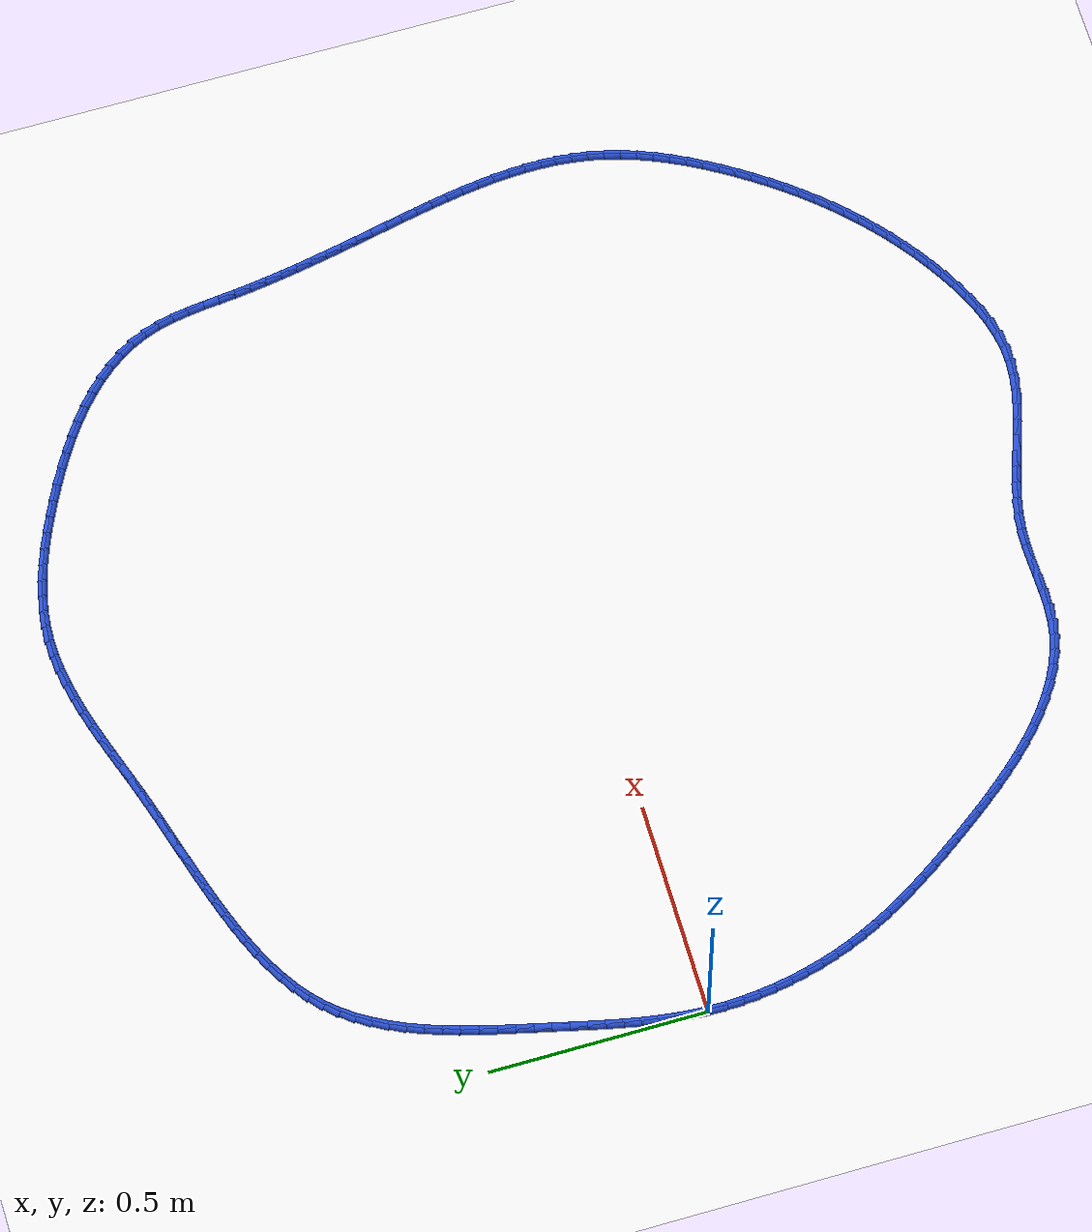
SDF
<sdf version="1.6">
 <world name="default">
  <light name="sun" type="directional">
   <pose>0 0 10 0 -0 0</pose>
   <diffuse>0.8 0.8 0.8 1</diffuse>
   <specular>0.2 0.2 0.2 1</specular>
   <attenuation>
    <range>1000</range>
    <constant>0.9</constant>
    <linear>0.01</linear>
    <quadratic>0.001</quadratic>
   </attenuation>
   <direction>-0.5 0.1 -0.9</direction>
  </light>
  <model name="ground_plane">
   <static>1</static>
   <link name="link">
    <collision name="collision">
     <geometry><plane><normal>0 0 1</normal><size>100 100</size></plane></geometry>
     <surface><friction><ode><mu>100</mu><mu2>50</mu2></ode></friction></surface>
    </collision>
    <visual name="visual">
     <cast_shadows>0</cast_shadows>
     <geometry><plane><normal>0 0 1</normal><size>100 100</size></plane></geometry>
     <material>
      <script><uri>file://media/materials/scripts/gazebo.material</uri><name>Gazebo/WhiteGlow</name></script>
     </material>
    </visual>
   </link>
  </model>
  <gravity>0 0 -9.8</gravity>
  <magnetic_field>6e-06 2.3e-05 -4.2e-05</magnetic_field>
  <atmosphere type="adiabatic"/>
  <physics name="default_physics" default="0" type="ode">
   <max_step_size>0.001</max_step_size>
   <real_time_factor>1</real_time_factor>
   <real_time_update_rate>1000</real_time_update_rate>
  </physics>
  <scene><ambient>0.4 0.4 0.4 1</ambient><background>0.7 0.7 0.7 1</background><shadows>1</shadows></scene>
  <spherical_coordinates>
   <surface_model>EARTH_WGS84</surface_model>
   <latitude_deg>0</latitude_deg>
   <longitude_deg>0</longitude_deg>
   <elevation>0</elevation>
   <heading_deg>0</heading_deg>
  </spherical_coordinates>
  <model name="line">
   <link name="link_0">
    <pose>-1.734723475976807e-18 2.7755575615628914e-17 0.01 0 1.57 1.517671566461461</pose>
    <collision name="collision">
     <geometry><cylinder><radius>0.01</radius><length>0.08</length></cylinder></geometry>
    </collision>
    <visual name="visual">
     <material>
      <script><name>Gazebo/Blue</name><uri>file://media/materials/scripts/gazebo.material</uri></script>
     </material>
     <geometry><cylinder><radius>0.01</radius><length>0.08</length></cylinder></geometry>
    </visual>
   </link>
   <link name="link_1">
    <pose>0.002012668439115579 0.037850046925808234 0.01 0 1.57 1.473999858505459</pose>
    <collision name="collision">
     <geometry><cylinder><radius>0.01</radius><length>0.08</length></cylinder></geometry>
    </collision>
    <visual name="visual">
     <material>
      <script><name>Gazebo/Blue</name><uri>file://media/materials/scripts/gazebo.material</uri></script>
     </material>
     <geometry><cylinder><radius>0.01</radius><length>0.08</length></cylinder></geometry>
    </visual>
   </link>
   <link name="link_2">
    <pose>0.005663176768669164 0.07544542671056687 0.01 0 1.57 1.4359093881045173</pose>
    <collision name="collision">
     <geometry><cylinder><radius>0.01</radius><length>0.08</length></cylinder></geometry>
    </collision>
    <visual name="visual">
     <material>
      <script><name>Gazebo/Blue</name><uri>file://media/materials/scripts/gazebo.material</uri></script>
     </material>
     <geometry><cylinder><radius>0.01</radius><length>0.08</length></cylinder></geometry>
    </visual>
   </link>
   <link name="link_3">
    <pose>0.01074241363078174 0.11287228789891261 0.01 0 1.57 1.4037001705646406</pose>
    <collision name="collision">
     <geometry><cylinder><radius>0.01</radius><length>0.08</length></cylinder></geometry>
    </collision>
    <visual name="visual">
     <material>
      <script><name>Gazebo/Blue</name><uri>file://media/materials/scripts/gazebo.material</uri></script>
     </material>
     <geometry><cylinder><radius>0.01</radius><length>0.08</length></cylinder></geometry>
    </visual>
   </link>
   <link name="link_4">
    <pose>0.017041267667574342 0.1502167790354822 0.01 0 1.57 1.3775309544224736</pose>
    <collision name="collision">
     <geometry><cylinder><radius>0.01</radius><length>0.08</length></cylinder></geometry>
    </collision>
    <visual name="visual">
     <material>
      <script><name>Gazebo/Blue</name><uri>file://media/materials/scripts/gazebo.material</uri></script>
     </material>
     <geometry><cylinder><radius>0.01</radius><length>0.08</length></cylinder></geometry>
    </visual>
   </link>
   <link name="link_5">
    <pose>0.024350627521167942 0.18756504866491217 0.01 0 1.57 1.3574494974719742</pose>
    <collision name="collision">
     <geometry><cylinder><radius>0.01</radius><length>0.08</length></cylinder></geometry>
    </collision>
    <visual name="visual">
     <material>
      <script><name>Gazebo/Blue</name><uri>file://media/materials/scripts/gazebo.material</uri></script>
     </material>
     <geometry><cylinder><radius>0.01</radius><length>0.08</length></cylinder></geometry>
    </visual>
   </link>
   <link name="link_6">
    <pose>0.032461381833683564 0.22500324533183938 0.01 0 1.57 1.3434215271262457</pose>
    <collision name="collision">
     <geometry><cylinder><radius>0.01</radius><length>0.08</length></cylinder></geometry>
    </collision>
    <visual name="visual">
     <material>
      <script><name>Gazebo/Blue</name><uri>file://media/materials/scripts/gazebo.material</uri></script>
     </material>
     <geometry><cylinder><radius>0.01</radius><length>0.08</length></cylinder></geometry>
    </visual>
   </link>
   <link name="link_7">
    <pose>0.04116441924724221 0.2626175175809003 0.01 0 1.57 1.3353549472956125</pose>
    <collision name="collision">
     <geometry><cylinder><radius>0.01</radius><length>0.08</length></cylinder></geometry>
    </collision>
    <visual name="visual">
     <material>
      <script><name>Gazebo/Blue</name><uri>file://media/materials/scripts/gazebo.material</uri></script>
     </material>
     <geometry><cylinder><radius>0.01</radius><length>0.08</length></cylinder></geometry>
    </visual>
   </link>
   <link name="link_8">
    <pose>0.05025062840396489 0.3004940139567318 0.01 0 1.57 1.333117686528782</pose>
    <collision name="collision">
     <geometry><cylinder><radius>0.01</radius><length>0.08</length></cylinder></geometry>
    </collision>
    <visual name="visual">
     <material>
      <script><name>Gazebo/Blue</name><uri>file://media/materials/scripts/gazebo.material</uri></script>
     </material>
     <geometry><cylinder><radius>0.01</radius><length>0.08</length></cylinder></geometry>
    </visual>
   </link>
   <link name="link_9">
    <pose>0.0595108979459726 0.3387188830039704 0.01 0 1.57 1.3350403573465852</pose>
    <collision name="collision">
     <geometry><cylinder><radius>0.01</radius><length>0.08</length></cylinder></geometry>
    </collision>
    <visual name="visual">
     <material>
      <script><name>Gazebo/Blue</name><uri>file://media/materials/scripts/gazebo.material</uri></script>
     </material>
     <geometry><cylinder><radius>0.01</radius><length>0.08</length></cylinder></geometry>
    </visual>
   </link>
   <link name="link_10">
    <pose>0.06878865346334007 0.37734028732001806 0.01 0 1.57 1.333252057619819</pose>
    <collision name="collision">
     <geometry><cylinder><radius>0.01</radius><length>0.08</length></cylinder></geometry>
    </collision>
    <visual name="visual">
     <material>
      <script><name>Gazebo/Blue</name><uri>file://media/materials/scripts/gazebo.material</uri></script>
     </material>
     <geometry><cylinder><radius>0.01</radius><length>0.08</length></cylinder></geometry>
    </visual>
   </link>
   <link name="link_11">
    <pose>0.0781995118509111 0.4162095862058645 0.01 0 1.57 1.3253046601133345</pose>
    <collision name="collision">
     <geometry><cylinder><radius>0.01</radius><length>0.08</length></cylinder></geometry>
    </collision>
    <visual name="visual">
     <material>
      <script><name>Gazebo/Blue</name><uri>file://media/materials/scripts/gazebo.material</uri></script>
     </material>
     <geometry><cylinder><radius>0.01</radius><length>0.08</length></cylinder></geometry>
    </visual>
   </link>
   <link name="link_12">
    <pose>0.08794697299528703 0.4551145966590776 0.01 0 1.57 1.3111583156858582</pose>
    <collision name="collision">
     <geometry><cylinder><radius>0.01</radius><length>0.08</length></cylinder></geometry>
    </collision>
    <visual name="visual">
     <material>
      <script><name>Gazebo/Blue</name><uri>file://media/materials/scripts/gazebo.material</uri></script>
     </material>
     <geometry><cylinder><radius>0.01</radius><length>0.08</length></cylinder></geometry>
    </visual>
   </link>
   <link name="link_13">
    <pose>0.09823458032457176 0.493843104195282 0.01 0 1.57 1.290639156370649</pose>
    <collision name="collision">
     <geometry><cylinder><radius>0.01</radius><length>0.08</length></cylinder></geometry>
    </collision>
    <visual name="visual">
     <material>
      <script><name>Gazebo/Blue</name><uri>file://media/materials/scripts/gazebo.material</uri></script>
     </material>
     <geometry><cylinder><radius>0.01</radius><length>0.08</length></cylinder></geometry>
    </visual>
   </link>
   <link name="link_14">
    <pose>0.10926587726686911 0.532182894330102 0.01 0 1.57 1.263448441039871</pose>
    <collision name="collision">
     <geometry><cylinder><radius>0.01</radius><length>0.08</length></cylinder></geometry>
    </collision>
    <visual name="visual">
     <material>
      <script><name>Gazebo/Blue</name><uri>file://media/materials/scripts/gazebo.material</uri></script>
     </material>
     <geometry><cylinder><radius>0.01</radius><length>0.08</length></cylinder></geometry>
    </visual>
   </link>
   <link name="link_15">
    <pose>0.12124440725028303 0.5699217525791623 0.01 0 1.57 1.2291768824134819</pose>
    <collision name="collision">
     <geometry><cylinder><radius>0.01</radius><length>0.08</length></cylinder></geometry>
    </collision>
    <visual name="visual">
     <material>
      <script><name>Gazebo/Blue</name><uri>file://media/materials/scripts/gazebo.material</uri></script>
     </material>
     <geometry><cylinder><radius>0.01</radius><length>0.08</length></cylinder></geometry>
    </visual>
   </link>
   <link name="link_16">
    <pose>0.1343737137029174 0.6068474644580875 0.01 0 1.57 1.1873282245700671</pose>
    <collision name="collision">
     <geometry><cylinder><radius>0.01</radius><length>0.08</length></cylinder></geometry>
    </collision>
    <visual name="visual">
     <material>
      <script><name>Gazebo/Blue</name><uri>file://media/materials/scripts/gazebo.material</uri></script>
     </material>
     <geometry><cylinder><radius>0.01</radius><length>0.08</length></cylinder></geometry>
    </visual>
   </link>
   <link name="link_17">
    <pose>0.14885734005287604 0.6427478154825018 0.01 0 1.57 1.137359574336715</pose>
    <collision name="collision">
     <geometry><cylinder><radius>0.01</radius><length>0.08</length></cylinder></geometry>
    </collision>
    <visual name="visual">
     <material>
      <script><name>Gazebo/Blue</name><uri>file://media/materials/scripts/gazebo.material</uri></script>
     </material>
     <geometry><cylinder><radius>0.01</radius><length>0.08</length></cylinder></geometry>
    </visual>
   </link>
   <link name="link_18">
    <pose>0.16489882972826295 0.67741059116803 0.01 0 1.57 1.0787479608447574</pose>
    <collision name="collision">
     <geometry><cylinder><radius>0.01</radius><length>0.08</length></cylinder></geometry>
    </collision>
    <visual name="visual">
     <material>
      <script><name>Gazebo/Blue</name><uri>file://media/materials/scripts/gazebo.material</uri></script>
     </material>
     <geometry><cylinder><radius>0.01</radius><length>0.08</length></cylinder></geometry>
    </visual>
   </link>
   <link name="link_19">
    <pose>0.18270172615718192 0.7106235770302967 0.01 0 1.57 1.0110927604278672</pose>
    <collision name="collision">
     <geometry><cylinder><radius>0.01</radius><length>0.08</length></cylinder></geometry>
    </collision>
    <visual name="visual">
     <material>
      <script><name>Gazebo/Blue</name><uri>file://media/materials/scripts/gazebo.material</uri></script>
     </material>
     <geometry><cylinder><radius>0.01</radius><length>0.08</length></cylinder></geometry>
    </visual>
   </link>
   <link name="link_20">
    <pose>0.20246957276773692 0.7421745585849262 0.01 0 1.57 0.9342588750147812</pose>
    <collision name="collision">
     <geometry><cylinder><radius>0.01</radius><length>0.08</length></cylinder></geometry>
    </collision>
    <visual name="visual">
     <material>
      <script><name>Gazebo/Blue</name><uri>file://media/materials/scripts/gazebo.material</uri></script>
     </material>
     <geometry><cylinder><radius>0.01</radius><length>0.08</length></cylinder></geometry>
    </visual>
   </link>
   <link name="link_21">
    <pose>0.22440591298803178 0.7718513213475431 0.01 0 1.57 0.8485517188159636</pose>
    <collision name="collision">
     <geometry><cylinder><radius>0.01</radius><length>0.08</length></cylinder></geometry>
    </collision>
    <visual name="visual">
     <material>
      <script><name>Gazebo/Blue</name><uri>file://media/materials/scripts/gazebo.material</uri></script>
     </material>
     <geometry><cylinder><radius>0.01</radius><length>0.08</length></cylinder></geometry>
    </visual>
   </link>
   <link name="link_22">
    <pose>0.24871429024617048 0.7994416508337719 0.01 0 1.57 0.7560578348984001</pose>
    <collision name="collision">
     <geometry><cylinder><radius>0.01</radius><length>0.08</length></cylinder></geometry>
    </collision>
    <visual name="visual">
     <material>
      <script><name>Gazebo/Blue</name><uri>file://media/materials/scripts/gazebo.material</uri></script>
     </material>
     <geometry><cylinder><radius>0.01</radius><length>0.08</length></cylinder></geometry>
    </visual>
   </link>
   <link name="link_23">
    <pose>0.27556357802786163 0.8247598869639315 0.01 0 1.57 0.6685631152657541</pose>
    <collision name="collision">
     <geometry><cylinder><radius>0.01</radius><length>0.08</length></cylinder></geometry>
    </collision>
    <visual name="visual">
     <material>
      <script><name>Gazebo/Blue</name><uri>file://media/materials/scripts/gazebo.material</uri></script>
     </material>
     <geometry><cylinder><radius>0.01</radius><length>0.08</length></cylinder></geometry>
    </visual>
   </link>
   <link name="link_24">
    <pose>0.30480850271612625 0.8478609812291112 0.01 0 1.57 0.5920031116642797</pose>
    <collision name="collision">
     <geometry><cylinder><radius>0.01</radius><length>0.08</length></cylinder></geometry>
    </collision>
    <visual name="visual">
     <material>
      <script><name>Gazebo/Blue</name><uri>file://media/materials/scripts/gazebo.material</uri></script>
     </material>
     <geometry><cylinder><radius>0.01</radius><length>0.08</length></cylinder></geometry>
    </visual>
   </link>
   <link name="link_25">
    <pose>0.33613663167671015 0.8689279155665567 0.01 0 1.57 0.5260467315800115</pose>
    <collision name="collision">
     <geometry><cylinder><radius>0.01</radius><length>0.08</length></cylinder></geometry>
    </collision>
    <visual name="visual">
     <material>
      <script><name>Gazebo/Blue</name><uri>file://media/materials/scripts/gazebo.material</uri></script>
     </material>
     <geometry><cylinder><radius>0.01</radius><length>0.08</length></cylinder></geometry>
    </visual>
   </link>
   <link name="link_26">
    <pose>0.3692339810309937 0.8881448600427045 0.01 0 1.57 0.4699905539958062</pose>
    <collision name="collision">
     <geometry><cylinder><radius>0.01</radius><length>0.08</length></cylinder></geometry>
    </collision>
    <visual name="visual">
     <material>
      <script><name>Gazebo/Blue</name><uri>file://media/materials/scripts/gazebo.material</uri></script>
     </material>
     <geometry><cylinder><radius>0.01</radius><length>0.08</length></cylinder></geometry>
    </visual>
   </link>
   <link name="link_27">
    <pose>0.40378656690035686 0.9056959847239914 0.01 0 1.57 0.42302276964865476</pose>
    <collision name="collision">
     <geometry><cylinder><radius>0.01</radius><length>0.08</length></cylinder></geometry>
    </collision>
    <visual name="visual">
     <material>
      <script><name>Gazebo/Blue</name><uri>file://media/materials/scripts/gazebo.material</uri></script>
     </material>
     <geometry><cylinder><radius>0.01</radius><length>0.08</length></cylinder></geometry>
    </visual>
   </link>
   <link name="link_28">
    <pose>0.43948040540618066 0.9217654596768546 0.01 0 1.57 0.38436100685794145</pose>
    <collision name="collision">
     <geometry><cylinder><radius>0.01</radius><length>0.08</length></cylinder></geometry>
    </collision>
    <visual name="visual">
     <material>
      <script><name>Gazebo/Blue</name><uri>file://media/materials/scripts/gazebo.material</uri></script>
     </material>
     <geometry><cylinder><radius>0.01</radius><length>0.08</length></cylinder></geometry>
    </visual>
   </link>
   <link name="link_29">
    <pose>0.47600151266984514 0.9365374549677308 0.01 0 1.57 0.3533335574357472</pose>
    <collision name="collision">
     <geometry><cylinder><radius>0.01</radius><length>0.08</length></cylinder></geometry>
    </collision>
    <visual name="visual">
     <material>
      <script><name>Gazebo/Blue</name><uri>file://media/materials/scripts/gazebo.material</uri></script>
     </material>
     <geometry><cylinder><radius>0.01</radius><length>0.08</length></cylinder></geometry>
    </visual>
   </link>
   <link name="link_30">
    <pose>0.5130359048127309 0.9501961406630569 0.01 0 1.57 0.32942492397430134</pose>
    <collision name="collision">
     <geometry><cylinder><radius>0.01</radius><length>0.08</length></cylinder></geometry>
    </collision>
    <visual name="visual">
     <material>
      <script><name>Gazebo/Blue</name><uri>file://media/materials/scripts/gazebo.material</uri></script>
     </material>
     <geometry><cylinder><radius>0.01</radius><length>0.08</length></cylinder></geometry>
    </visual>
   </link>
   <link name="link_31">
    <pose>0.550269597956218 0.9629256868292702 0.01 0 1.57 0.31227396458008644</pose>
    <collision name="collision">
     <geometry><cylinder><radius>0.01</radius><length>0.08</length></cylinder></geometry>
    </collision>
    <visual name="visual">
     <material>
      <script><name>Gazebo/Blue</name><uri>file://media/materials/scripts/gazebo.material</uri></script>
     </material>
     <geometry><cylinder><radius>0.01</radius><length>0.08</length></cylinder></geometry>
    </visual>
   </link>
   <link name="link_32">
    <pose>0.5873918816709613 0.9749101198948988 0.01 0 1.57 0.3004222368947837</pose>
    <collision name="collision">
     <geometry><cylinder><radius>0.01</radius><length>0.08</length></cylinder></geometry>
    </collision>
    <visual name="visual">
     <material>
      <script><name>Gazebo/Blue</name><uri>file://media/materials/scripts/gazebo.material</uri></script>
     </material>
     <geometry><cylinder><radius>0.01</radius><length>0.08</length></cylinder></geometry>
    </visual>
   </link>
   <link name="link_33">
    <pose>0.6242438051991526 0.9863268071225759 0.01 0 1.57 0.2921180132417486</pose>
    <collision name="collision">
     <geometry><cylinder><radius>0.01</radius><length>0.08</length></cylinder></geometry>
    </collision>
    <visual name="visual">
     <material>
      <script><name>Gazebo/Blue</name><uri>file://media/materials/scripts/gazebo.material</uri></script>
     </material>
     <geometry><cylinder><radius>0.01</radius><length>0.08</length></cylinder></geometry>
    </visual>
   </link>
   <link name="link_34">
    <pose>0.6608790374420357 0.9973437860922326 0.01 0 1.57 0.2873832606052084</pose>
    <collision name="collision">
     <geometry><cylinder><radius>0.01</radius><length>0.08</length></cylinder></geometry>
    </collision>
    <visual name="visual">
     <material>
      <script><name>Gazebo/Blue</name><uri>file://media/materials/scripts/gazebo.material</uri></script>
     </material>
     <geometry><cylinder><radius>0.01</radius><length>0.08</length></cylinder></geometry>
    </visual>
   </link>
   <link name="link_35">
    <pose>0.6973671282826666 1.0081283975313928 0.01 0 1.57 0.28631972677840295</pose>
    <collision name="collision">
     <geometry><cylinder><radius>0.01</radius><length>0.08</length></cylinder></geometry>
    </collision>
    <visual name="visual">
     <material>
      <script><name>Gazebo/Blue</name><uri>file://media/materials/scripts/gazebo.material</uri></script>
     </material>
     <geometry><cylinder><radius>0.01</radius><length>0.08</length></cylinder></geometry>
    </visual>
   </link>
   <link name="link_36">
    <pose>0.7337776276041006 1.01884798216758 0.01 0 1.57 0.28896395803367747</pose>
    <collision name="collision">
     <geometry><cylinder><radius>0.01</radius><length>0.08</length></cylinder></geometry>
    </collision>
    <visual name="visual">
     <material>
      <script><name>Gazebo/Blue</name><uri>file://media/materials/scripts/gazebo.material</uri></script>
     </material>
     <geometry><cylinder><radius>0.01</radius><length>0.08</length></cylinder></geometry>
    </visual>
   </link>
   <link name="link_37">
    <pose>0.7701800852893932 1.0296698807283178 0.01 0 1.57 0.2952858270425174</pose>
    <collision name="collision">
     <geometry><cylinder><radius>0.01</radius><length>0.08</length></cylinder></geometry>
    </collision>
    <visual name="visual">
     <material>
      <script><name>Gazebo/Blue</name><uri>file://media/materials/scripts/gazebo.material</uri></script>
     </material>
     <geometry><cylinder><radius>0.01</radius><length>0.08</length></cylinder></geometry>
    </visual>
   </link>
   <link name="link_38">
    <pose>0.8066440512215998 1.0407614339411295 0.01 0 1.57 0.3051885678288169</pose>
    <collision name="collision">
     <geometry><cylinder><radius>0.01</radius><length>0.08</length></cylinder></geometry>
    </collision>
    <visual name="visual">
     <material>
      <script><name>Gazebo/Blue</name><uri>file://media/materials/scripts/gazebo.material</uri></script>
     </material>
     <geometry><cylinder><radius>0.01</radius><length>0.08</length></cylinder></geometry>
    </visual>
   </link>
   <link name="link_39">
    <pose>0.8432390752837764 1.0522899825335394 0.01 0 1.57 0.31721759130286614</pose>
    <collision name="collision">
     <geometry><cylinder><radius>0.01</radius><length>0.08</length></cylinder></geometry>
    </collision>
    <visual name="visual">
     <material>
      <script><name>Gazebo/Blue</name><uri>file://media/materials/scripts/gazebo.material</uri></script>
     </material>
     <geometry><cylinder><radius>0.01</radius><length>0.08</length></cylinder></geometry>
    </visual>
   </link>
   <link name="link_40">
    <pose>0.88002293678208 1.064366281406955 0.01 0 1.57 0.3240960358654579</pose>
    <collision name="collision">
     <geometry><cylinder><radius>0.01</radius><length>0.08</length></cylinder></geometry>
    </collision>
    <visual name="visual">
     <material>
      <script><name>Gazebo/Blue</name><uri>file://media/materials/scripts/gazebo.material</uri></script>
     </material>
     <geometry><cylinder><radius>0.01</radius><length>0.08</length></cylinder></geometry>
    </visual>
   </link>
   <link name="link_41">
    <pose>0.9169875011613049 1.0767842114191495 0.01 0 1.57 0.3234907469065928</pose>
    <collision name="collision">
     <geometry><cylinder><radius>0.01</radius><length>0.08</length></cylinder></geometry>
    </collision>
    <visual name="visual">
     <material>
      <script><name>Gazebo/Blue</name><uri>file://media/materials/scripts/gazebo.material</uri></script>
     </material>
     <geometry><cylinder><radius>0.01</radius><length>0.08</length></cylinder></geometry>
    </visual>
   </link>
   <link name="link_42">
    <pose>0.9541017030330773 1.0892274158287019 0.01 0 1.57 0.315479203527795</pose>
    <collision name="collision">
     <geometry><cylinder><radius>0.01</radius><length>0.08</length></cylinder></geometry>
    </collision>
    <visual name="visual">
     <material>
      <script><name>Gazebo/Blue</name><uri>file://media/materials/scripts/gazebo.material</uri></script>
     </material>
     <geometry><cylinder><radius>0.01</radius><length>0.08</length></cylinder></geometry>
    </visual>
   </link>
   <link name="link_43">
    <pose>0.9913344538489507 1.1013794265545507 0.01 0 1.57 0.29999644888421784</pose>
    <collision name="collision">
     <geometry><cylinder><radius>0.01</radius><length>0.08</length></cylinder></geometry>
    </collision>
    <visual name="visual">
     <material>
      <script><name>Gazebo/Blue</name><uri>file://media/materials/scripts/gazebo.material</uri></script>
     </material>
     <geometry><cylinder><radius>0.01</radius><length>0.08</length></cylinder></geometry>
    </visual>
   </link>
   <link name="link_44">
    <pose>1.028654665060478 1.112923775515634 0.01 0 1.57 0.2768444939718171</pose>
    <collision name="collision">
     <geometry><cylinder><radius>0.01</radius><length>0.08</length></cylinder></geometry>
    </collision>
    <visual name="visual">
     <material>
      <script><name>Gazebo/Blue</name><uri>file://media/materials/scripts/gazebo.material</uri></script>
     </material>
     <geometry><cylinder><radius>0.01</radius><length>0.08</length></cylinder></geometry>
    </visual>
   </link>
   <link name="link_45">
    <pose>1.0660312481192138 1.1235439946308918 0.01 0 1.57 0.24571217159944497</pose>
    <collision name="collision">
     <geometry><cylinder><radius>0.01</radius><length>0.08</length></cylinder></geometry>
    </collision>
    <visual name="visual">
     <material>
      <script><name>Gazebo/Blue</name><uri>file://media/materials/scripts/gazebo.material</uri></script>
     </material>
     <geometry><cylinder><radius>0.01</radius><length>0.08</length></cylinder></geometry>
    </visual>
   </link>
   <link name="link_46">
    <pose>1.103433114476712 1.1329236158192615 0.01 0 1.57 0.20620790659444546</pose>
    <collision name="collision">
     <geometry><cylinder><radius>0.01</radius><length>0.08</length></cylinder></geometry>
    </collision>
    <visual name="visual">
     <material>
      <script><name>Gazebo/Blue</name><uri>file://media/materials/scripts/gazebo.material</uri></script>
     </material>
     <geometry><cylinder><radius>0.01</radius><length>0.08</length></cylinder></geometry>
    </visual>
   </link>
   <link name="link_47">
    <pose>1.140829175584525 1.1407461709996822 0.01 0 1.57 0.15791276877775526</pose>
    <collision name="collision">
     <geometry><cylinder><radius>0.01</radius><length>0.08</length></cylinder></geometry>
    </collision>
    <visual name="visual">
     <material>
      <script><name>Gazebo/Blue</name><uri>file://media/materials/scripts/gazebo.material</uri></script>
     </material>
     <geometry><cylinder><radius>0.01</radius><length>0.08</length></cylinder></geometry>
    </visual>
   </link>
   <link name="link_48">
    <pose>1.1781883428942073 1.1466951920910924 0.01 0 1.57 0.10046246006281516</pose>
    <collision name="collision">
     <geometry><cylinder><radius>0.01</radius><length>0.08</length></cylinder></geometry>
    </collision>
    <visual name="visual">
     <material>
      <script><name>Gazebo/Blue</name><uri>file://media/materials/scripts/gazebo.material</uri></script>
     </material>
     <geometry><cylinder><radius>0.01</radius><length>0.08</length></cylinder></geometry>
    </visual>
   </link>
   <link name="link_49">
    <pose>1.2154795278573132 1.1504542110124312 0.01 0 1.57 0.03366507871410601</pose>
    <collision name="collision">
     <geometry><cylinder><radius>0.01</radius><length>0.08</length></cylinder></geometry>
    </collision>
    <visual name="visual">
     <material>
      <script><name>Gazebo/Blue</name><uri>file://media/materials/scripts/gazebo.material</uri></script>
     </material>
     <geometry><cylinder><radius>0.01</radius><length>0.08</length></cylinder></geometry>
    </visual>
   </link>
   <link name="link_50">
    <pose>1.2526716419253952 1.1517067596826362 0.01 0 1.57 -0.04173460928842841</pose>
    <collision name="collision">
     <geometry><cylinder><radius>0.01</radius><length>0.08</length></cylinder></geometry>
    </collision>
    <visual name="visual">
     <material>
      <script><name>Gazebo/Blue</name><uri>file://media/materials/scripts/gazebo.material</uri></script>
     </material>
     <geometry><cylinder><radius>0.01</radius><length>0.08</length></cylinder></geometry>
    </visual>
   </link>
   <link name="link_51">
    <pose>1.2897353893636805 1.150159019954036 0.01 0 1.57 -0.11694974476046575</pose>
    <collision name="collision">
     <geometry><cylinder><radius>0.01</radius><length>0.08</length></cylinder></geometry>
    </collision>
    <visual name="visual">
     <material>
      <script><name>Gazebo/Blue</name><uri>file://media/materials/scripts/gazebo.material</uri></script>
     </material>
     <geometry><cylinder><radius>0.01</radius><length>0.08</length></cylinder></geometry>
    </visual>
   </link>
   <link name="link_52">
    <pose>1.3266654645382308 1.1458202582627384 0.01 0 1.57 -0.18541950344100522</pose>
    <collision name="collision">
     <geometry><cylinder><radius>0.01</radius><length>0.08</length></cylinder></geometry>
    </collision>
    <visual name="visual">
     <material>
      <script><name>Gazebo/Blue</name><uri>file://media/materials/scripts/gazebo.material</uri></script>
     </material>
     <geometry><cylinder><radius>0.01</radius><length>0.08</length></cylinder></geometry>
    </visual>
   </link>
   <link name="link_53">
    <pose>1.3634736787378738 1.138915991716248 0.01 0 1.57 -0.24664395707683806</pose>
    <collision name="collision">
     <geometry><cylinder><radius>0.01</radius><length>0.08</length></cylinder></geometry>
    </collision>
    <visual name="visual">
     <material>
      <script><name>Gazebo/Blue</name><uri>file://media/materials/scripts/gazebo.material</uri></script>
     </material>
     <geometry><cylinder><radius>0.01</radius><length>0.08</length></cylinder></geometry>
    </visual>
   </link>
   <link name="link_54">
    <pose>1.400172212135153 1.1296763978012774 0.01 0 1.57 -0.30056637683307386</pose>
    <collision name="collision">
     <geometry><cylinder><radius>0.01</radius><length>0.08</length></cylinder></geometry>
    </collision>
    <visual name="visual">
     <material>
      <script><name>Gazebo/Blue</name><uri>file://media/materials/scripts/gazebo.material</uri></script>
     </material>
     <geometry><cylinder><radius>0.01</radius><length>0.08</length></cylinder></geometry>
    </visual>
   </link>
   <link name="link_55">
    <pose>1.4367732449026118 1.1183316540045396 0.01 0 1.57 -0.34734988757907026</pose>
    <collision name="collision">
     <geometry><cylinder><radius>0.01</radius><length>0.08</length></cylinder></geometry>
    </collision>
    <visual name="visual">
     <material>
      <script><name>Gazebo/Blue</name><uri>file://media/materials/scripts/gazebo.material</uri></script>
     </material>
     <geometry><cylinder><radius>0.01</radius><length>0.08</length></cylinder></geometry>
    </visual>
   </link>
   <link name="link_56">
    <pose>1.473288957212792 1.1051119378127479 0.01 0 1.57 -0.38728837506278063</pose>
    <collision name="collision">
     <geometry><cylinder><radius>0.01</radius><length>0.08</length></cylinder></geometry>
    </collision>
    <visual name="visual">
     <material>
      <script><name>Gazebo/Blue</name><uri>file://media/materials/scripts/gazebo.material</uri></script>
     </material>
     <geometry><cylinder><radius>0.01</radius><length>0.08</length></cylinder></geometry>
    </visual>
   </link>
   <link name="link_57">
    <pose>1.5097315292382372 1.0902474267126157 0.01 0 1.57 -0.42073535850950294</pose>
    <collision name="collision">
     <geometry><cylinder><radius>0.01</radius><length>0.08</length></cylinder></geometry>
    </collision>
    <visual name="visual">
     <material>
      <script><name>Gazebo/Blue</name><uri>file://media/materials/scripts/gazebo.material</uri></script>
     </material>
     <geometry><cylinder><radius>0.01</radius><length>0.08</length></cylinder></geometry>
    </visual>
   </link>
   <link name="link_58">
    <pose>1.5461131411514906 1.0739682981908554 0.01 0 1.57 -0.44805325515489186</pose>
    <collision name="collision">
     <geometry><cylinder><radius>0.01</radius><length>0.08</length></cylinder></geometry>
    </collision>
    <visual name="visual">
     <material>
      <script><name>Gazebo/Blue</name><uri>file://media/materials/scripts/gazebo.material</uri></script>
     </material>
     <geometry><cylinder><radius>0.01</radius><length>0.08</length></cylinder></geometry>
    </visual>
   </link>
   <link name="link_59">
    <pose>1.5824459473849004 1.0565047054050667 0.01 0 1.57 -0.47163703341844565</pose>
    <collision name="collision">
     <geometry><cylinder><radius>0.01</radius><length>0.08</length></cylinder></geometry>
    </collision>
    <visual name="visual">
     <material>
      <script><name>Gazebo/Blue</name><uri>file://media/materials/scripts/gazebo.material</uri></script>
     </material>
     <geometry><cylinder><radius>0.01</radius><length>0.08</length></cylinder></geometry>
    </visual>
   </link>
   <link name="link_60">
    <pose>1.6186774263969883 1.0380256710820541 0.01 0 1.57 -0.4982961547250398</pose>
    <collision name="collision">
     <geometry><cylinder><radius>0.01</radius><length>0.08</length></cylinder></geometry>
    </collision>
    <visual name="visual">
     <material>
      <script><name>Gazebo/Blue</name><uri>file://media/materials/scripts/gazebo.material</uri></script>
     </material>
     <geometry><cylinder><radius>0.01</radius><length>0.08</length></cylinder></geometry>
    </visual>
   </link>
   <link name="link_61">
    <pose>1.6545508603557815 1.0185072157181858 0.01 0 1.57 -0.5296776074510986</pose>
    <collision name="collision">
     <geometry><cylinder><radius>0.01</radius><length>0.08</length></cylinder></geometry>
    </collision>
    <visual name="visual">
     <material>
      <script><name>Gazebo/Blue</name><uri>file://media/materials/scripts/gazebo.material</uri></script>
     </material>
     <geometry><cylinder><radius>0.01</radius><length>0.08</length></cylinder></geometry>
    </visual>
   </link>
   <link name="link_62">
    <pose>1.689769331394532 0.9978873635447824 0.01 0 1.57 -0.5662557525745743</pose>
    <collision name="collision">
     <geometry><cylinder><radius>0.01</radius><length>0.08</length></cylinder></geometry>
    </collision>
    <visual name="visual">
     <material>
      <script><name>Gazebo/Blue</name><uri>file://media/materials/scripts/gazebo.material</uri></script>
     </material>
     <geometry><cylinder><radius>0.01</radius><length>0.08</length></cylinder></geometry>
    </visual>
   </link>
   <link name="link_63">
    <pose>1.724035921646493 0.9761041387931646 0.01 0 1.57 -0.6086112892046317</pose>
    <collision name="collision">
     <geometry><cylinder><radius>0.01</radius><length>0.08</length></cylinder></geometry>
    </collision>
    <visual name="visual">
     <material>
      <script><name>Gazebo/Blue</name><uri>file://media/materials/scripts/gazebo.material</uri></script>
     </material>
     <geometry><cylinder><radius>0.01</radius><length>0.08</length></cylinder></geometry>
    </visual>
   </link>
   <link name="link_64">
    <pose>1.757053713244916 0.9530955656946529 0.01 0 1.57 -0.6574222308709009</pose>
    <collision name="collision">
     <geometry><cylinder><radius>0.01</radius><length>0.08</length></cylinder></geometry>
    </collision>
    <visual name="visual">
     <material>
      <script><name>Gazebo/Blue</name><uri>file://media/materials/scripts/gazebo.material</uri></script>
     </material>
     <geometry><cylinder><radius>0.01</radius><length>0.08</length></cylinder></geometry>
    </visual>
   </link>
   <link name="link_65">
    <pose>1.7885257883230536 0.9287996684805685 0.01 0 1.57 -0.7134417483590566</pose>
    <collision name="collision">
     <geometry><cylinder><radius>0.01</radius><length>0.08</length></cylinder></geometry>
    </collision>
    <visual name="visual">
     <material>
      <script><name>Gazebo/Blue</name><uri>file://media/materials/scripts/gazebo.material</uri></script>
     </material>
     <geometry><cylinder><radius>0.01</radius><length>0.08</length></cylinder></geometry>
    </visual>
   </link>
   <link name="link_66">
    <pose>1.818155229014159 0.9031544713822317 0.01 0 1.57 -0.7774525084432803</pose>
    <collision name="collision">
     <geometry><cylinder><radius>0.01</radius><length>0.08</length></cylinder></geometry>
    </collision>
    <visual name="visual">
     <material>
      <script><name>Gazebo/Blue</name><uri>file://media/materials/scripts/gazebo.material</uri></script>
     </material>
     <geometry><cylinder><radius>0.01</radius><length>0.08</length></cylinder></geometry>
    </visual>
   </link>
   <link name="link_67">
    <pose>1.8456451174514825 0.8760979986309632 0.01 0 1.57 -0.8501842268915573</pose>
    <collision name="collision">
     <geometry><cylinder><radius>0.01</radius><length>0.08</length></cylinder></geometry>
    </collision>
    <visual name="visual">
     <material>
      <script><name>Gazebo/Blue</name><uri>file://media/materials/scripts/gazebo.material</uri></script>
     </material>
     <geometry><cylinder><radius>0.01</radius><length>0.08</length></cylinder></geometry>
    </visual>
   </link>
   <link name="link_68">
    <pose>1.8706985357682784 0.8475682744580842 0.01 0 1.57 -0.9321810528416091</pose>
    <collision name="collision">
     <geometry><cylinder><radius>0.01</radius><length>0.08</length></cylinder></geometry>
    </collision>
    <visual name="visual">
     <material>
      <script><name>Gazebo/Blue</name><uri>file://media/materials/scripts/gazebo.material</uri></script>
     </material>
     <geometry><cylinder><radius>0.01</radius><length>0.08</length></cylinder></geometry>
    </visual>
   </link>
   <link name="link_69">
    <pose>1.893018566097798 0.8175033230949147 0.01 0 1.57 -1.023613307756846</pose>
    <collision name="collision">
     <geometry><cylinder><radius>0.01</radius><length>0.08</length></cylinder></geometry>
    </collision>
    <visual name="visual">
     <material>
      <script><name>Gazebo/Blue</name><uri>file://media/materials/scripts/gazebo.material</uri></script>
     </material>
     <geometry><cylinder><radius>0.01</radius><length>0.08</length></cylinder></geometry>
    </visual>
   </link>
   <link name="link_70">
    <pose>1.9123082905732935 0.7858411687727761 0.01 0 1.57 -1.1240507909081565</pose>
    <collision name="collision">
     <geometry><cylinder><radius>0.01</radius><length>0.08</length></cylinder></geometry>
    </collision>
    <visual name="visual">
     <material>
      <script><name>Gazebo/Blue</name><uri>file://media/materials/scripts/gazebo.material</uri></script>
     </material>
     <geometry><cylinder><radius>0.01</radius><length>0.08</length></cylinder></geometry>
    </visual>
   </link>
   <link name="link_71">
    <pose>1.9282707913280188 0.7525198357229888 0.01 0 1.57 -1.2308119848595287</pose>
    <collision name="collision">
     <geometry><cylinder><radius>0.01</radius><length>0.08</length></cylinder></geometry>
    </collision>
    <visual name="visual">
     <material>
      <script><name>Gazebo/Blue</name><uri>file://media/materials/scripts/gazebo.material</uri></script>
     </material>
     <geometry><cylinder><radius>0.01</radius><length>0.08</length></cylinder></geometry>
    </visual>
   </link>
   <link name="link_72">
    <pose>1.9406587793571084 0.71749774503529 0.01 0 1.57 -1.3244775293441966</pose>
    <collision name="collision">
     <geometry><cylinder><radius>0.01</radius><length>0.08</length></cylinder></geometry>
    </collision>
    <visual name="visual">
     <material>
      <script><name>Gazebo/Blue</name><uri>file://media/materials/scripts/gazebo.material</uri></script>
     </material>
     <geometry><cylinder><radius>0.01</radius><length>0.08</length></cylinder></geometry>
    </visual>
   </link>
   <link name="link_73">
    <pose>1.9498388212014712 0.6809856049601504 0.01 0 1.57 -1.3931888268229862</pose>
    <collision name="collision">
     <geometry><cylinder><radius>0.01</radius><length>0.08</length></cylinder></geometry>
    </collision>
    <visual name="visual">
     <material>
      <script><name>Gazebo/Blue</name><uri>file://media/materials/scripts/gazebo.material</uri></script>
     </material>
     <geometry><cylinder><radius>0.01</radius><length>0.08</length></cylinder></geometry>
    </visual>
   </link>
   <link name="link_74">
    <pose>1.9565917857942763 0.6433643969905791 0.01 0 1.57 -1.43820079650926</pose>
    <collision name="collision">
     <geometry><cylinder><radius>0.01</radius><length>0.08</length></cylinder></geometry>
    </collision>
    <visual name="visual">
     <material>
      <script><name>Gazebo/Blue</name><uri>file://media/materials/scripts/gazebo.material</uri></script>
     </material>
     <geometry><cylinder><radius>0.01</radius><length>0.08</length></cylinder></geometry>
    </visual>
   </link>
   <link name="link_75">
    <pose>1.9617063161896533 0.6050182976887155 0.01 0 1.57 -1.4610021049767237</pose>
    <collision name="collision">
     <geometry><cylinder><radius>0.01</radius><length>0.08</length></cylinder></geometry>
    </collision>
    <visual name="visual">
     <material>
      <script><name>Gazebo/Blue</name><uri>file://media/materials/scripts/gazebo.material</uri></script>
     </material>
     <geometry><cylinder><radius>0.01</radius><length>0.08</length></cylinder></geometry>
    </visual>
   </link>
   <link name="link_76">
    <pose>1.965971055441732 0.5663314836166985 0.01 0 1.57 -1.4624436191215349</pose>
    <collision name="collision">
     <geometry><cylinder><radius>0.01</radius><length>0.08</length></cylinder></geometry>
    </collision>
    <visual name="visual">
     <material>
      <script><name>Gazebo/Blue</name><uri>file://media/materials/scripts/gazebo.material</uri></script>
     </material>
     <geometry><cylinder><radius>0.01</radius><length>0.08</length></cylinder></geometry>
    </visual>
   </link>
   <link name="link_77">
    <pose>1.9701746314856892 0.5276881232768644 0.01 0 1.57 -1.4469496289792643</pose>
    <collision name="collision">
     <geometry><cylinder><radius>0.01</radius><length>0.08</length></cylinder></geometry>
    </collision>
    <visual name="visual">
     <material>
      <script><name>Gazebo/Blue</name><uri>file://media/materials/scripts/gazebo.material</uri></script>
     </material>
     <geometry><cylinder><radius>0.01</radius><length>0.08</length></cylinder></geometry>
    </visual>
   </link>
   <link name="link_78">
    <pose>1.9749426874496498 0.4893854991753003 0.01 0 1.57 -1.4297063557068674</pose>
    <collision name="collision">
     <geometry><cylinder><radius>0.01</radius><length>0.08</length></cylinder></geometry>
    </collision>
    <visual name="visual">
     <material>
      <script><name>Gazebo/Blue</name><uri>file://media/materials/scripts/gazebo.material</uri></script>
     </material>
     <geometry><cylinder><radius>0.01</radius><length>0.08</length></cylinder></geometry>
    </visual>
   </link>
   <link name="link_79">
    <pose>1.9803351634622235 0.45141932172935556 0.01 0 1.57 -1.4141518859821052</pose>
    <collision name="collision">
     <geometry><cylinder><radius>0.01</radius><length>0.08</length></cylinder></geometry>
    </collision>
    <visual name="visual">
     <material>
      <script><name>Gazebo/Blue</name><uri>file://media/materials/scripts/gazebo.material</uri></script>
     </material>
     <geometry><cylinder><radius>0.01</radius><length>0.08</length></cylinder></geometry>
    </visual>
   </link>
   <link name="link_80">
    <pose>1.9862893459251423 0.4137199155609395 0.01 0 1.57 -1.400391045977205</pose>
    <collision name="collision">
     <geometry><cylinder><radius>0.01</radius><length>0.08</length></cylinder></geometry>
    </collision>
    <visual name="visual">
     <material>
      <script><name>Gazebo/Blue</name><uri>file://media/materials/scripts/gazebo.material</uri></script>
     </material>
     <geometry><cylinder><radius>0.01</radius><length>0.08</length></cylinder></geometry>
    </visual>
   </link>
   <link name="link_81">
    <pose>1.9927425212401368 0.37621760529196285 0.01 0 1.57 -1.3885088139259074</pose>
    <collision name="collision">
     <geometry><cylinder><radius>0.01</radius><length>0.08</length></cylinder></geometry>
    </collision>
    <visual name="visual">
     <material>
      <script><name>Gazebo/Blue</name><uri>file://media/materials/scripts/gazebo.material</uri></script>
     </material>
     <geometry><cylinder><radius>0.01</radius><length>0.08</length></cylinder></geometry>
    </visual>
   </link>
   <link name="link_82">
    <pose>1.9996319758089396 0.3388427155443355 0.01 0 1.57 -1.3785699237883078</pose>
    <collision name="collision">
     <geometry><cylinder><radius>0.01</radius><length>0.08</length></cylinder></geometry>
    </collision>
    <visual name="visual">
     <material>
      <script><name>Gazebo/Blue</name><uri>file://media/materials/scripts/gazebo.material</uri></script>
     </material>
     <geometry><cylinder><radius>0.01</radius><length>0.08</length></cylinder></geometry>
    </visual>
   </link>
   <link name="link_83">
    <pose>2.0068949960332816 0.3015255709399668 0.01 0 1.57 -1.370618935664239</pose>
    <collision name="collision">
     <geometry><cylinder><radius>0.01</radius><length>0.08</length></cylinder></geometry>
    </collision>
    <visual name="visual">
     <material>
      <script><name>Gazebo/Blue</name><uri>file://media/materials/scripts/gazebo.material</uri></script>
     </material>
     <geometry><cylinder><radius>0.01</radius><length>0.08</length></cylinder></geometry>
    </visual>
   </link>
   <link name="link_84">
    <pose>2.0144688683148946 0.2641964961007674 0.01 0 1.57 -1.3646806818856114</pose>
    <collision name="collision">
     <geometry><cylinder><radius>0.01</radius><length>0.08</length></cylinder></geometry>
    </collision>
    <visual name="visual">
     <material>
      <script><name>Gazebo/Blue</name><uri>file://media/materials/scripts/gazebo.material</uri></script>
     </material>
     <geometry><cylinder><radius>0.01</radius><length>0.08</length></cylinder></geometry>
    </visual>
   </link>
   <link name="link_85">
    <pose>2.02229087905551 0.22678581564864675 0.01 0 1.57 -1.3607609977910289</pose>
    <collision name="collision">
     <geometry><cylinder><radius>0.01</radius><length>0.08</length></cylinder></geometry>
    </collision>
    <visual name="visual">
     <material>
      <script><name>Gazebo/Blue</name><uri>file://media/materials/scripts/gazebo.material</uri></script>
     </material>
     <geometry><cylinder><radius>0.01</radius><length>0.08</length></cylinder></geometry>
    </visual>
   </link>
   <link name="link_86">
    <pose>2.0302983146568603 0.18922385420551546 0.01 0 1.57 -1.3588638479744435</pose>
    <collision name="collision">
     <geometry><cylinder><radius>0.01</radius><length>0.08</length></cylinder></geometry>
    </collision>
    <visual name="visual">
     <material>
      <script><name>Gazebo/Blue</name><uri>file://media/materials/scripts/gazebo.material</uri></script>
     </material>
     <geometry><cylinder><radius>0.01</radius><length>0.08</length></cylinder></geometry>
    </visual>
   </link>
   <link name="link_87">
    <pose>2.0384276413668503 0.15144177306357073 0.01 0 1.57 -1.35982373584555</pose>
    <collision name="collision">
     <geometry><cylinder><radius>0.01</radius><length>0.08</length></cylinder></geometry>
    </collision>
    <visual name="visual">
     <material>
      <script><name>Gazebo/Blue</name><uri>file://media/materials/scripts/gazebo.material</uri></script>
     </material>
     <geometry><cylinder><radius>0.01</radius><length>0.08</length></cylinder></geometry>
    </visual>
   </link>
   <link name="link_88">
    <pose>2.046571293857328 0.11341565180991643 0.01 0 1.57 -1.36487557884351</pose>
    <collision name="collision">
     <geometry><cylinder><radius>0.01</radius><length>0.08</length></cylinder></geometry>
    </collision>
    <visual name="visual">
     <material>
      <script><name>Gazebo/Blue</name><uri>file://media/materials/scripts/gazebo.material</uri></script>
     </material>
     <geometry><cylinder><radius>0.01</radius><length>0.08</length></cylinder></geometry>
    </visual>
   </link>
   <link name="link_89">
    <pose>2.05455627937079 0.07518831505488328 0.01 0 1.57 -1.374103525408147</pose>
    <collision name="collision">
     <geometry><cylinder><radius>0.01</radius><length>0.08</length></cylinder></geometry>
    </collision>
    <visual name="visual">
     <material>
      <script><name>Gazebo/Blue</name><uri>file://media/materials/scripts/gazebo.material</uri></script>
     </material>
     <geometry><cylinder><radius>0.01</radius><length>0.08</length></cylinder></geometry>
    </visual>
   </link>
   <link name="link_90">
    <pose>2.0622042943077754 0.03680800520181235 0.01 0 1.57 -1.3875377576266903</pose>
    <collision name="collision">
     <geometry><cylinder><radius>0.01</radius><length>0.08</length></cylinder></geometry>
    </collision>
    <visual name="visual">
     <material>
      <script><name>Gazebo/Blue</name><uri>file://media/materials/scripts/gazebo.material</uri></script>
     </material>
     <geometry><cylinder><radius>0.01</radius><length>0.08</length></cylinder></geometry>
    </visual>
   </link>
   <link name="link_91">
    <pose>2.0693370350688283 -0.0016770353459547851 0.01 0 1.57 -1.4052544913835636</pose>
    <collision name="collision">
     <geometry><cylinder><radius>0.01</radius><length>0.08</length></cylinder></geometry>
    </collision>
    <visual name="visual">
     <material>
      <script><name>Gazebo/Blue</name><uri>file://media/materials/scripts/gazebo.material</uri></script>
     </material>
     <geometry><cylinder><radius>0.01</radius><length>0.08</length></cylinder></geometry>
    </visual>
   </link>
   <link name="link_92">
    <pose>2.0757761980544895 -0.04021856418507734 0.01 0 1.57 -1.4273699613599242</pose>
    <collision name="collision">
     <geometry><cylinder><radius>0.01</radius><length>0.08</length></cylinder></geometry>
    </collision>
    <visual name="visual">
     <material>
      <script><name>Gazebo/Blue</name><uri>file://media/materials/scripts/gazebo.material</uri></script>
     </material>
     <geometry><cylinder><radius>0.01</radius><length>0.08</length></cylinder></geometry>
    </visual>
   </link>
   <link name="link_93">
    <pose>2.0813434796653 -0.07876833891221233 0.01 0 1.57 -1.4540324872274775</pose>
    <collision name="collision">
     <geometry><cylinder><radius>0.01</radius><length>0.08</length></cylinder></geometry>
    </collision>
    <visual name="visual">
     <material>
      <script><name>Gazebo/Blue</name><uri>file://media/materials/scripts/gazebo.material</uri></script>
     </material>
     <geometry><cylinder><radius>0.01</radius><length>0.08</length></cylinder></geometry>
    </visual>
   </link>
   <link name="link_94">
    <pose>2.085860576301803 -0.11727811712401898 0.01 0 1.57 -1.4854116098977035</pose>
    <collision name="collision">
     <geometry><cylinder><radius>0.01</radius><length>0.08</length></cylinder></geometry>
    </collision>
    <visual name="visual">
     <material>
      <script><name>Gazebo/Blue</name><uri>file://media/materials/scripts/gazebo.material</uri></script>
     </material>
     <geometry><cylinder><radius>0.01</radius><length>0.08</length></cylinder></geometry>
    </visual>
   </link>
   <link name="link_95">
    <pose>2.089149184364539 -0.15569965641715564 0.01 0 1.57 -1.5216831035784686</pose>
    <collision name="collision">
     <geometry><cylinder><radius>0.01</radius><length>0.08</length></cylinder></geometry>
    </collision>
    <visual name="visual">
     <material>
      <script><name>Gazebo/Blue</name><uri>file://media/materials/scripts/gazebo.material</uri></script>
     </material>
     <geometry><cylinder><radius>0.01</radius><length>0.08</length></cylinder></geometry>
    </visual>
   </link>
   <link name="link_96">
    <pose>2.09103100025405 -0.1939847143882809 0.01 0 1.57 -1.5630086229820446</pose>
    <collision name="collision">
     <geometry><cylinder><radius>0.01</radius><length>0.08</length></cylinder></geometry>
    </collision>
    <visual name="visual">
     <material>
      <script><name>Gazebo/Blue</name><uri>file://media/materials/scripts/gazebo.material</uri></script>
     </material>
     <geometry><cylinder><radius>0.01</radius><length>0.08</length></cylinder></geometry>
    </visual>
   </link>
   <link name="link_97">
    <pose>2.0913277203708778 -0.23208504863405321 0.01 0 1.57 1.5320836682283179</pose>
    <collision name="collision">
     <geometry><cylinder><radius>0.01</radius><length>0.08</length></cylinder></geometry>
    </collision>
    <visual name="visual">
     <material>
      <script><name>Gazebo/Blue</name><uri>file://media/materials/scripts/gazebo.material</uri></script>
     </material>
     <geometry><cylinder><radius>0.01</radius><length>0.08</length></cylinder></geometry>
    </visual>
   </link>
   <link name="link_98">
    <pose>2.0898610411155647 -0.2699524167511319 0.01 0 1.57 1.4803618293123737</pose>
    <collision name="collision">
     <geometry><cylinder><radius>0.01</radius><length>0.08</length></cylinder></geometry>
    </collision>
    <visual name="visual">
     <material>
      <script><name>Gazebo/Blue</name><uri>file://media/materials/scripts/gazebo.material</uri></script>
     </material>
     <geometry><cylinder><radius>0.01</radius><length>0.08</length></cylinder></geometry>
    </visual>
   </link>
   <link name="link_99">
    <pose>2.0864526588886516 -0.30753857633617376 0.01 0 1.57 1.423484846382992</pose>
    <collision name="collision">
     <geometry><cylinder><radius>0.01</radius><length>0.08</length></cylinder></geometry>
    </collision>
    <visual name="visual">
     <material>
      <script><name>Gazebo/Blue</name><uri>file://media/materials/scripts/gazebo.material</uri></script>
     </material>
     <geometry><cylinder><radius>0.01</radius><length>0.08</length></cylinder></geometry>
    </visual>
   </link>
   <link name="link_100">
    <pose>2.0809242700906805 -0.344795284985838 0.01 0 1.57 1.3617723974587643</pose>
    <collision name="collision">
     <geometry><cylinder><radius>0.01</radius><length>0.08</length></cylinder></geometry>
    </collision>
    <visual name="visual">
     <material>
      <script><name>Gazebo/Blue</name><uri>file://media/materials/scripts/gazebo.material</uri></script>
     </material>
     <geometry><cylinder><radius>0.01</radius><length>0.08</length></cylinder></geometry>
    </visual>
   </link>
   <link name="link_101">
    <pose>2.073101367989571 -0.38167450137056996 0.01 0 1.57 1.2996330340256246</pose>
    <collision name="collision">
     <geometry><cylinder><radius>0.01</radius><length>0.08</length></cylinder></geometry>
    </collision>
    <visual name="visual">
     <material>
      <script><name>Gazebo/Blue</name><uri>file://media/materials/scripts/gazebo.material</uri></script>
     </material>
     <geometry><cylinder><radius>0.01</radius><length>0.08</length></cylinder></geometry>
    </visual>
   </link>
   <link name="link_102">
    <pose>2.0629645618026182 -0.4181363987620128 0.01 0 1.57 1.2425895240601776</pose>
    <collision name="collision">
     <geometry><cylinder><radius>0.01</radius><length>0.08</length></cylinder></geometry>
    </collision>
    <visual name="visual">
     <material>
      <script><name>Gazebo/Blue</name><uri>file://media/materials/scripts/gazebo.material</uri></script>
     </material>
     <geometry><cylinder><radius>0.01</radius><length>0.08</length></cylinder></geometry>
    </visual>
   </link>
   <link name="link_103">
    <pose>2.0507004191260667 -0.45415205753680754 0.01 0 1.57 1.1909161917558324</pose>
    <collision name="collision">
     <geometry><cylinder><radius>0.01</radius><length>0.08</length></cylinder></geometry>
    </collision>
    <visual name="visual">
     <material>
      <script><name>Gazebo/Blue</name><uri>file://media/materials/scripts/gazebo.material</uri></script>
     </material>
     <geometry><cylinder><radius>0.01</radius><length>0.08</length></cylinder></geometry>
    </visual>
   </link>
   <link name="link_104">
    <pose>2.036509729795163 -0.48969331125024357 0.01 0 1.57 1.1444107724059973</pose>
    <collision name="collision">
     <geometry><cylinder><radius>0.01</radius><length>0.08</length></cylinder></geometry>
    </collision>
    <visual name="visual">
     <material>
      <script><name>Gazebo/Blue</name><uri>file://media/materials/scripts/gazebo.material</uri></script>
     </material>
     <geometry><cylinder><radius>0.01</radius><length>0.08</length></cylinder></geometry>
    </visual>
   </link>
   <link name="link_105">
    <pose>2.020593283645155 -0.5247319934576135 0.01 0 1.57 1.1028127085200135</pose>
    <collision name="collision">
     <geometry><cylinder><radius>0.01</radius><length>0.08</length></cylinder></geometry>
    </collision>
    <visual name="visual">
     <material>
      <script><name>Gazebo/Blue</name><uri>file://media/materials/scripts/gazebo.material</uri></script>
     </material>
     <geometry><cylinder><radius>0.01</radius><length>0.08</length></cylinder></geometry>
    </visual>
   </link>
   <link name="link_106">
    <pose>2.003151870511288 -0.5592399377142084 0.01 0 1.57 1.065838411165277</pose>
    <collision name="collision">
     <geometry><cylinder><radius>0.01</radius><length>0.08</length></cylinder></geometry>
    </collision>
    <visual name="visual">
     <material>
      <script><name>Gazebo/Blue</name><uri>file://media/materials/scripts/gazebo.material</uri></script>
     </material>
     <geometry><cylinder><radius>0.01</radius><length>0.08</length></cylinder></geometry>
    </visual>
   </link>
   <link name="link_107">
    <pose>1.9843862802288084 -0.5931889775753194 0.01 0 1.57 1.0332072154840328</pose>
    <collision name="collision">
     <geometry><cylinder><radius>0.01</radius><length>0.08</length></cylinder></geometry>
    </collision>
    <visual name="visual">
     <material>
      <script><name>Gazebo/Blue</name><uri>file://media/materials/scripts/gazebo.material</uri></script>
     </material>
     <geometry><cylinder><radius>0.01</radius><length>0.08</length></cylinder></geometry>
    </visual>
   </link>
   <link name="link_108">
    <pose>1.9644973026329642 -0.6265509465962384 0.01 0 1.57 1.0046505965355876</pose>
    <collision name="collision">
     <geometry><cylinder><radius>0.01</radius><length>0.08</length></cylinder></geometry>
    </collision>
    <visual name="visual">
     <material>
      <script><name>Gazebo/Blue</name><uri>file://media/materials/scripts/gazebo.material</uri></script>
     </material>
     <geometry><cylinder><radius>0.01</radius><length>0.08</length></cylinder></geometry>
    </visual>
   </link>
   <link name="link_109">
    <pose>1.9436853172113278 -0.6592976643949715 0.01 0 1.57 0.9784916603497278</pose>
    <collision name="collision">
     <geometry><cylinder><radius>0.01</radius><length>0.08</length></cylinder></geometry>
    </collision>
    <visual name="visual">
     <material>
      <script><name>Gazebo/Blue</name><uri>file://media/materials/scripts/gazebo.material</uri></script>
     </material>
     <geometry><cylinder><radius>0.01</radius><length>0.08</length></cylinder></geometry>
    </visual>
   </link>
   <link name="link_110">
    <pose>1.9220845701000353 -0.6913987043981695 0.01 0 1.57 0.9515873185597096</pose>
    <collision name="collision">
     <geometry><cylinder><radius>0.01</radius><length>0.08</length></cylinder></geometry>
    </collision>
    <visual name="visual">
     <material>
      <script><name>Gazebo/Blue</name><uri>file://media/materials/scripts/gazebo.material</uri></script>
     </material>
     <geometry><cylinder><radius>0.01</radius><length>0.08</length></cylinder></geometry>
    </visual>
   </link>
   <link name="link_111">
    <pose>1.8996908808169635 -0.7228189384308522 0.01 0 1.57 0.9235450106625145</pose>
    <collision name="collision">
     <geometry><cylinder><radius>0.01</radius><length>0.08</length></cylinder></geometry>
    </collision>
    <visual name="visual">
     <material>
      <script><name>Gazebo/Blue</name><uri>file://media/materials/scripts/gazebo.material</uri></script>
     </material>
     <geometry><cylinder><radius>0.01</radius><length>0.08</length></cylinder></geometry>
    </visual>
   </link>
   <link name="link_112">
    <pose>1.8764826761483366 -0.753522647581253 0.01 0 1.57 0.8943654853542936</pose>
    <collision name="collision">
     <geometry><cylinder><radius>0.01</radius><length>0.08</length></cylinder></geometry>
    </collision>
    <visual name="visual">
     <material>
      <script><name>Gazebo/Blue</name><uri>file://media/materials/scripts/gazebo.material</uri></script>
     </material>
     <geometry><cylinder><radius>0.01</radius><length>0.08</length></cylinder></geometry>
    </visual>
   </link>
   <link name="link_113">
    <pose>1.8524383828803805 -0.7834741129376054 0.01 0 1.57 0.8640575323885824</pose>
    <collision name="collision">
     <geometry><cylinder><radius>0.01</radius><length>0.08</length></cylinder></geometry>
    </collision>
    <visual name="visual">
     <material>
      <script><name>Gazebo/Blue</name><uri>file://media/materials/scripts/gazebo.material</uri></script>
     </material>
     <geometry><cylinder><radius>0.01</radius><length>0.08</length></cylinder></geometry>
    </visual>
   </link>
   <link name="link_114">
    <pose>1.8275364277993174 -0.8126376155881425 0.01 0 1.57 0.8326391002740492</pose>
    <collision name="collision">
     <geometry><cylinder><radius>0.01</radius><length>0.08</length></cylinder></geometry>
    </collision>
    <visual name="visual">
     <material>
      <script><name>Gazebo/Blue</name><uri>file://media/materials/scripts/gazebo.material</uri></script>
     </material>
     <geometry><cylinder><radius>0.01</radius><length>0.08</length></cylinder></geometry>
    </visual>
   </link>
   <link name="link_115">
    <pose>1.8017552376913728 -0.8409774366210988 0.01 0 1.57 0.8001383531054367</pose>
    <collision name="collision">
     <geometry><cylinder><radius>0.01</radius><length>0.08</length></cylinder></geometry>
    </collision>
    <visual name="visual">
     <material>
      <script><name>Gazebo/Blue</name><uri>file://media/materials/scripts/gazebo.material</uri></script>
     </material>
     <geometry><cylinder><radius>0.01</radius><length>0.08</length></cylinder></geometry>
    </visual>
   </link>
   <link name="link_116">
    <pose>1.7750732393427717 -0.8684578571247061 0.01 0 1.57 0.7665946086437836</pose>
    <collision name="collision">
     <geometry><cylinder><radius>0.01</radius><length>0.08</length></cylinder></geometry>
    </collision>
    <visual name="visual">
     <material>
      <script><name>Gazebo/Blue</name><uri>file://media/materials/scripts/gazebo.material</uri></script>
     </material>
     <geometry><cylinder><radius>0.01</radius><length>0.08</length></cylinder></geometry>
    </visual>
   </link>
   <link name="link_117">
    <pose>1.7474688595397385 -0.895043158187199 0.01 0 1.57 0.7320590926888093</pose>
    <collision name="collision">
     <geometry><cylinder><radius>0.01</radius><length>0.08</length></cylinder></geometry>
    </collision>
    <visual name="visual">
     <material>
      <script><name>Gazebo/Blue</name><uri>file://media/materials/scripts/gazebo.material</uri></script>
     </material>
     <geometry><cylinder><radius>0.01</radius><length>0.08</length></cylinder></geometry>
    </visual>
   </link>
   <link name="link_118">
    <pose>1.718920525068497 -0.9206976208968102 0.01 0 1.57 0.6965954412610812</pose>
    <collision name="collision">
     <geometry><cylinder><radius>0.01</radius><length>0.08</length></cylinder></geometry>
    </collision>
    <visual name="visual">
     <material>
      <script><name>Gazebo/Blue</name><uri>file://media/materials/scripts/gazebo.material</uri></script>
     </material>
     <geometry><cylinder><radius>0.01</radius><length>0.08</length></cylinder></geometry>
    </visual>
   </link>
   <link name="link_119">
    <pose>1.6894066627152717 -0.9453855263417734 0.01 0 1.57 0.6602798835986974</pose>
    <collision name="collision">
     <geometry><cylinder><radius>0.01</radius><length>0.08</length></cylinder></geometry>
    </collision>
    <visual name="visual">
     <material>
      <script><name>Gazebo/Blue</name><uri>file://media/materials/scripts/gazebo.material</uri></script>
     </material>
     <geometry><cylinder><radius>0.01</radius><length>0.08</length></cylinder></geometry>
    </visual>
   </link>
   <link name="link_120">
    <pose>1.658905699266287 -0.9690711556103228 0.01 0 1.57 0.6232010467264986</pose>
    <collision name="collision">
     <geometry><cylinder><radius>0.01</radius><length>0.08</length></cylinder></geometry>
    </collision>
    <visual name="visual">
     <material>
      <script><name>Gazebo/Blue</name><uri>file://media/materials/scripts/gazebo.material</uri></script>
     </material>
     <geometry><cylinder><radius>0.01</radius><length>0.08</length></cylinder></geometry>
    </visual>
   </link>
   <link name="link_121">
    <pose>1.6273960615077683 -0.9917187897906907 0.01 0 1.57 0.5854593370964976</pose>
    <collision name="collision">
     <geometry><cylinder><radius>0.01</radius><length>0.08</length></cylinder></geometry>
    </collision>
    <visual name="visual">
     <material>
      <script><name>Gazebo/Blue</name><uri>file://media/materials/scripts/gazebo.material</uri></script>
     </material>
     <geometry><cylinder><radius>0.01</radius><length>0.08</length></cylinder></geometry>
    </visual>
   </link>
   <link name="link_122">
    <pose>1.5948561762259392 -1.013292709971111 0.01 0 1.57 0.547132905321613</pose>
    <collision name="collision">
     <geometry><cylinder><radius>0.01</radius><length>0.08</length></cylinder></geometry>
    </collision>
    <visual name="visual">
     <material>
      <script><name>Gazebo/Blue</name><uri>file://media/materials/scripts/gazebo.material</uri></script>
     </material>
     <geometry><cylinder><radius>0.01</radius><length>0.08</length></cylinder></geometry>
    </visual>
   </link>
   <link name="link_123">
    <pose>1.5612653639040677 -1.0337551342450626 0.01 0 1.57 0.5056141817886866</pose>
    <collision name="collision">
     <geometry><cylinder><radius>0.01</radius><length>0.08</length></cylinder></geometry>
    </collision>
    <visual name="visual">
     <material>
      <script><name>Gazebo/Blue</name><uri>file://media/materials/scripts/gazebo.material</uri></script>
     </material>
     <geometry><cylinder><radius>0.01</radius><length>0.08</length></cylinder></geometry>
    </visual>
   </link>
   <link name="link_124">
    <pose>1.5266733369904821 -1.0529057891147955 0.01 0 1.57 0.4557072311325494</pose>
    <collision name="collision">
     <geometry><cylinder><radius>0.01</radius><length>0.08</length></cylinder></geometry>
    </collision>
    <visual name="visual">
     <material>
      <script><name>Gazebo/Blue</name><uri>file://media/materials/scripts/gazebo.material</uri></script>
     </material>
     <geometry><cylinder><radius>0.01</radius><length>0.08</length></cylinder></geometry>
    </visual>
   </link>
   <link name="link_125">
    <pose>1.491249837483556 -1.070267326951089 0.01 0 1.57 0.3956741168832094</pose>
    <collision name="collision">
     <geometry><cylinder><radius>0.01</radius><length>0.08</length></cylinder></geometry>
    </collision>
    <visual name="visual">
     <material>
      <script><name>Gazebo/Blue</name><uri>file://media/materials/scripts/gazebo.material</uri></script>
     </material>
     <geometry><cylinder><radius>0.01</radius><length>0.08</length></cylinder></geometry>
    </visual>
   </link>
   <link name="link_126">
    <pose>1.4551763237544568 -1.0853353542529809 0.01 0 1.57 0.3239516032862178</pose>
    <collision name="collision">
     <geometry><cylinder><radius>0.01</radius><length>0.08</length></cylinder></geometry>
    </collision>
    <visual name="visual">
     <material>
      <script><name>Gazebo/Blue</name><uri>file://media/materials/scripts/gazebo.material</uri></script>
     </material>
     <geometry><cylinder><radius>0.01</radius><length>0.08</length></cylinder></geometry>
    </visual>
   </link>
   <link name="link_127">
    <pose>1.4186342541743535 -1.0976054775195079 0.01 0 1.57 0.23884976242004316</pose>
    <collision name="collision">
     <geometry><cylinder><radius>0.01</radius><length>0.08</length></cylinder></geometry>
    </collision>
    <visual name="visual">
     <material>
      <script><name>Gazebo/Blue</name><uri>file://media/materials/scripts/gazebo.material</uri></script>
     </material>
     <geometry><cylinder><radius>0.01</radius><length>0.08</length></cylinder></geometry>
    </visual>
   </link>
   <link name="link_128">
    <pose>1.3818050871144139 -1.1065733032497078 0.01 0 1.57 0.1388373421225055</pose>
    <collision name="collision">
     <geometry><cylinder><radius>0.01</radius><length>0.08</length></cylinder></geometry>
    </collision>
    <visual name="visual">
     <material>
      <script><name>Gazebo/Blue</name><uri>file://media/materials/scripts/gazebo.material</uri></script>
     </material>
     <geometry><cylinder><radius>0.01</radius><length>0.08</length></cylinder></geometry>
    </visual>
   </link>
   <link name="link_129">
    <pose>1.3448702809458044 -1.1117344379426175 0.01 0 1.57 0.024803933862125285</pose>
    <collision name="collision">
     <geometry><cylinder><radius>0.01</radius><length>0.08</length></cylinder></geometry>
    </collision>
    <visual name="visual">
     <material>
      <script><name>Gazebo/Blue</name><uri>file://media/materials/scripts/gazebo.material</uri></script>
     </material>
     <geometry><cylinder><radius>0.01</radius><length>0.08</length></cylinder></geometry>
    </visual>
   </link>
   <link name="link_130">
    <pose>1.3079988574753059 -1.112649181893683 0.01 0 1.57 -0.08349620742181163</pose>
    <collision name="collision">
     <geometry><cylinder><radius>0.01</radius><length>0.08</length></cylinder></geometry>
    </collision>
    <visual name="visual">
     <material>
      <script><name>Gazebo/Blue</name><uri>file://media/materials/scripts/gazebo.material</uri></script>
     </material>
     <geometry><cylinder><radius>0.01</radius><length>0.08</length></cylinder></geometry>
    </visual>
   </link>
   <link name="link_131">
    <pose>1.2712264574106356 -1.1095716708819894 0.01 0 1.57 -0.1724104004024309</pose>
    <collision name="collision">
     <geometry><cylinder><radius>0.01</radius><length>0.08</length></cylinder></geometry>
    </collision>
    <visual name="visual">
     <material>
      <script><name>Gazebo/Blue</name><uri>file://media/materials/scripts/gazebo.material</uri></script>
     </material>
     <geometry><cylinder><radius>0.01</radius><length>0.08</length></cylinder></geometry>
    </visual>
   </link>
   <link name="link_132">
    <pose>1.2345077025121076 -1.103177493358355 0.01 0 1.57 -0.2411656977083214</pose>
    <collision name="collision">
     <geometry><cylinder><radius>0.01</radius><length>0.08</length></cylinder></geometry>
    </collision>
    <visual name="visual">
     <material>
      <script><name>Gazebo/Blue</name><uri>file://media/materials/scripts/gazebo.material</uri></script>
     </material>
     <geometry><cylinder><radius>0.01</radius><length>0.08</length></cylinder></geometry>
    </visual>
   </link>
   <link name="link_133">
    <pose>1.1977960733595585 -1.094148174083265 0.01 0 1.57 -0.2903987445344718</pose>
    <collision name="collision">
     <geometry><cylinder><radius>0.01</radius><length>0.08</length></cylinder></geometry>
    </collision>
    <visual name="visual">
     <material>
      <script><name>Gazebo/Blue</name><uri>file://media/materials/scripts/gazebo.material</uri></script>
     </material>
     <geometry><cylinder><radius>0.01</radius><length>0.08</length></cylinder></geometry>
    </visual>
   </link>
   <link name="link_134">
    <pose>1.1610450505328238 -1.0831652378172054 0.01 0 1.57 -0.3211652904059786</pose>
    <collision name="collision">
     <geometry><cylinder><radius>0.01</radius><length>0.08</length></cylinder></geometry>
    </collision>
    <visual name="visual">
     <material>
      <script><name>Gazebo/Blue</name><uri>file://media/materials/scripts/gazebo.material</uri></script>
     </material>
     <geometry><cylinder><radius>0.01</radius><length>0.08</length></cylinder></geometry>
    </visual>
   </link>
   <link name="link_135">
    <pose>1.1242081146117398 -1.0709102093206608 0.01 0 1.57 -0.33441551424580657</pose>
    <collision name="collision">
     <geometry><cylinder><radius>0.01</radius><length>0.08</length></cylinder></geometry>
    </collision>
    <visual name="visual">
     <material>
      <script><name>Gazebo/Blue</name><uri>file://media/materials/scripts/gazebo.material</uri></script>
     </material>
     <geometry><cylinder><radius>0.01</radius><length>0.08</length></cylinder></geometry>
    </visual>
   </link>
   <link name="link_136">
    <pose>1.0872387461761424 -1.0580646133541172 0.01 0 1.57 -0.3307325934585394</pose>
    <collision name="collision">
     <geometry><cylinder><radius>0.01</radius><length>0.08</length></cylinder></geometry>
    </collision>
    <visual name="visual">
     <material>
      <script><name>Gazebo/Blue</name><uri>file://media/materials/scripts/gazebo.material</uri></script>
     </material>
     <geometry><cylinder><radius>0.01</radius><length>0.08</length></cylinder></geometry>
    </visual>
   </link>
   <link name="link_137">
    <pose>1.050090425805868 -1.0453099746780594 0.01 0 1.57 -0.3102500039975654</pose>
    <collision name="collision">
     <geometry><cylinder><radius>0.01</radius><length>0.08</length></cylinder></geometry>
    </collision>
    <visual name="visual">
     <material>
      <script><name>Gazebo/Blue</name><uri>file://media/materials/scripts/gazebo.material</uri></script>
     </material>
     <geometry><cylinder><radius>0.01</radius><length>0.08</length></cylinder></geometry>
    </visual>
   </link>
   <link name="link_138">
    <pose>1.0127166340807539 -1.0333278180529737 0.01 0 1.57 -0.27269660300495874</pose>
    <collision name="collision">
     <geometry><cylinder><radius>0.01</radius><length>0.08</length></cylinder></geometry>
    </collision>
    <visual name="visual">
     <material>
      <script><name>Gazebo/Blue</name><uri>file://media/materials/scripts/gazebo.material</uri></script>
     </material>
     <geometry><cylinder><radius>0.01</radius><length>0.08</length></cylinder></geometry>
    </visual>
   </link>
   <link name="link_139">
    <pose>0.9750708515806357 -1.0227996682393448 0.01 0 1.57 -0.21756696297485953</pose>
    <collision name="collision">
     <geometry><cylinder><radius>0.01</radius><length>0.08</length></cylinder></geometry>
    </collision>
    <visual name="visual">
     <material>
      <script><name>Gazebo/Blue</name><uri>file://media/materials/scripts/gazebo.material</uri></script>
     </material>
     <geometry><cylinder><radius>0.01</radius><length>0.08</length></cylinder></geometry>
    </visual>
   </link>
   <link name="link_140">
    <pose>0.9371065588853498 -1.0144070499976585 0.01 0 1.57 -0.1444516068293377</pose>
    <collision name="collision">
     <geometry><cylinder><radius>0.01</radius><length>0.08</length></cylinder></geometry>
    </collision>
    <visual name="visual">
     <material>
      <script><name>Gazebo/Blue</name><uri>file://media/materials/scripts/gazebo.material</uri></script>
     </material>
     <geometry><cylinder><radius>0.01</radius><length>0.08</length></cylinder></geometry>
    </visual>
   </link>
   <link name="link_141">
    <pose>0.8987772372940798 -1.0088314834311627 0.01 0 1.57 -0.06236192708340401</pose>
    <collision name="collision">
     <geometry><cylinder><radius>0.01</radius><length>0.08</length></cylinder></geometry>
    </collision>
    <visual name="visual">
     <material>
      <script><name>Gazebo/Blue</name><uri>file://media/materials/scripts/gazebo.material</uri></script>
     </material>
     <geometry><cylinder><radius>0.01</radius><length>0.08</length></cylinder></geometry>
    </visual>
   </link>
   <link name="link_142">
    <pose>0.8600887029932 -1.006415659342568 0.01 0 1.57 -0.004442271133101755</pose>
    <collision name="collision">
     <geometry><cylinder><radius>0.01</radius><length>0.08</length></cylinder></geometry>
    </collision>
    <visual name="visual">
     <material>
      <script><name>Gazebo/Blue</name><uri>file://media/materials/scripts/gazebo.material</uri></script>
     </material>
     <geometry><cylinder><radius>0.01</radius><length>0.08</length></cylinder></geometry>
    </visual>
   </link>
   <link name="link_143">
    <pose>0.8212412627441554 -1.0062430873449877 0.01 0 1.57 0.02222871130980114</pose>
    <collision name="collision">
     <geometry><cylinder><radius>0.01</radius><length>0.08</length></cylinder></geometry>
    </collision>
    <visual name="visual">
     <material>
      <script><name>Gazebo/Blue</name><uri>file://media/materials/scripts/gazebo.material</uri></script>
     </material>
     <geometry><cylinder><radius>0.01</radius><length>0.08</length></cylinder></geometry>
    </visual>
   </link>
   <link name="link_144">
    <pose>0.782480393553718 -1.0071048334550818 0.01 0 1.57 0.017878691033953308</pose>
    <collision name="collision">
     <geometry><cylinder><radius>0.01</radius><length>0.08</length></cylinder></geometry>
    </collision>
    <visual name="visual">
     <material>
      <script><name>Gazebo/Blue</name><uri>file://media/materials/scripts/gazebo.material</uri></script>
     </material>
     <geometry><cylinder><radius>0.01</radius><length>0.08</length></cylinder></geometry>
    </visual>
   </link>
   <link name="link_145">
    <pose>0.7440515724286614 -1.0077919636895112 0.01 0 1.57 -0.018396755985960463</pose>
    <collision name="collision">
     <geometry><cylinder><radius>0.01</radius><length>0.08</length></cylinder></geometry>
    </collision>
    <visual name="visual">
     <material>
      <script><name>Gazebo/Blue</name><uri>file://media/materials/scripts/gazebo.material</uri></script>
     </material>
     <geometry><cylinder><radius>0.01</radius><length>0.08</length></cylinder></geometry>
    </visual>
   </link>
   <link name="link_146">
    <pose>0.7062002763757579 -1.0070955440649352 0.01 0 1.57 -0.08858888296789394</pose>
    <collision name="collision">
     <geometry><cylinder><radius>0.01</radius><length>0.08</length></cylinder></geometry>
    </collision>
    <visual name="visual">
     <material>
      <script><name>Gazebo/Blue</name><uri>file://media/materials/scripts/gazebo.material</uri></script>
     </material>
     <geometry><cylinder><radius>0.01</radius><length>0.08</length></cylinder></geometry>
    </visual>
   </link>
   <link name="link_147">
    <pose>0.6691719824017813 -1.0038066405980148 0.01 0 1.57 -0.1910376646948952</pose>
    <collision name="collision">
     <geometry><cylinder><radius>0.01</radius><length>0.08</length></cylinder></geometry>
    </collision>
    <visual name="visual">
     <material>
      <script><name>Gazebo/Blue</name><uri>file://media/materials/scripts/gazebo.material</uri></script>
     </material>
     <geometry><cylinder><radius>0.01</radius><length>0.08</length></cylinder></geometry>
    </visual>
   </link>
   <link name="link_148">
    <pose>0.6331881343400653 -0.9968475048120129 0.01 0 1.57 -0.2989433024306132</pose>
    <collision name="collision">
     <geometry><cylinder><radius>0.01</radius><length>0.08</length></cylinder></geometry>
    </collision>
    <visual name="visual">
     <material>
      <script><name>Gazebo/Blue</name><uri>file://media/materials/scripts/gazebo.material</uri></script>
     </material>
     <geometry><cylinder><radius>0.01</radius><length>0.08</length></cylinder></geometry>
    </visual>
   </link>
   <link name="link_149">
    <pose>0.5982954178634409 -0.9860943087716474 0.01 0 1.57 -0.3986346273005474</pose>
    <collision name="collision">
     <geometry><cylinder><radius>0.01</radius><length>0.08</length></cylinder></geometry>
    </collision>
    <visual name="visual">
     <material>
      <script><name>Gazebo/Blue</name><uri>file://media/materials/scripts/gazebo.material</uri></script>
     </material>
     <geometry><cylinder><radius>0.01</radius><length>0.08</length></cylinder></geometry>
    </visual>
   </link>
   <link name="link_150">
    <pose>0.5644632975835544 -0.9718447370837743 0.01 0 1.57 -0.48881231446988843</pose>
    <collision name="collision">
     <geometry><cylinder><radius>0.01</radius><length>0.08</length></cylinder></geometry>
    </collision>
    <visual name="visual">
     <material>
      <script><name>Gazebo/Blue</name><uri>file://media/materials/scripts/gazebo.material</uri></script>
     </material>
     <geometry><cylinder><radius>0.01</radius><length>0.08</length></cylinder></geometry>
    </visual>
   </link>
   <link name="link_151">
    <pose>0.5316608969467729 -0.9543983366120286 0.01 0 1.57 -0.569076832165642</pose>
    <collision name="collision">
     <geometry><cylinder><radius>0.01</radius><length>0.08</length></cylinder></geometry>
    </collision>
    <visual name="visual">
     <material>
      <script><name>Gazebo/Blue</name><uri>file://media/materials/scripts/gazebo.material</uri></script>
     </material>
     <geometry><cylinder><radius>0.01</radius><length>0.08</length></cylinder></geometry>
    </visual>
   </link>
   <link name="link_152">
    <pose>0.4998573393994627 -0.934054654220046 0.01 0 1.57 -0.6396445619077767</pose>
    <collision name="collision">
     <geometry><cylinder><radius>0.01</radius><length>0.08</length></cylinder></geometry>
    </collision>
    <visual name="visual">
     <material>
      <script><name>Gazebo/Blue</name><uri>file://media/materials/scripts/gazebo.material</uri></script>
     </material>
     <geometry><cylinder><radius>0.01</radius><length>0.08</length></cylinder></geometry>
    </visual>
   </link>
   <link name="link_153">
    <pose>0.46902174838799077 -0.9111132367714617 0.01 0 1.57 -0.7011033685772273</pose>
    <collision name="collision">
     <geometry><cylinder><radius>0.01</radius><length>0.08</length></cylinder></geometry>
    </collision>
    <visual name="visual">
     <material>
      <script><name>Gazebo/Blue</name><uri>file://media/materials/scripts/gazebo.material</uri></script>
     </material>
     <geometry><cylinder><radius>0.01</radius><length>0.08</length></cylinder></geometry>
    </visual>
   </link>
   <link name="link_154">
    <pose>0.4391232473587233 -0.8858736311299104 0.01 0 1.57 -0.7542145359895042</pose>
    <collision name="collision">
     <geometry><cylinder><radius>0.01</radius><length>0.08</length></cylinder></geometry>
    </collision>
    <visual name="visual">
     <material>
      <script><name>Gazebo/Blue</name><uri>file://media/materials/scripts/gazebo.material</uri></script>
     </material>
     <geometry><cylinder><radius>0.01</radius><length>0.08</length></cylinder></geometry>
    </visual>
   </link>
   <link name="link_155">
    <pose>0.41013095975802855 -0.8586353841590286 0.01 0 1.57 -0.7997762959732352</pose>
    <collision name="collision">
     <geometry><cylinder><radius>0.01</radius><length>0.08</length></cylinder></geometry>
    </collision>
    <visual name="visual">
     <material>
      <script><name>Gazebo/Blue</name><uri>file://media/materials/scripts/gazebo.material</uri></script>
     </material>
     <geometry><cylinder><radius>0.01</radius><length>0.08</length></cylinder></geometry>
    </visual>
   </link>
   <link name="link_156">
    <pose>0.3820140090322723 -0.8296980427224512 0.01 0 1.57 -0.8385407828625183</pose>
    <collision name="collision">
     <geometry><cylinder><radius>0.01</radius><length>0.08</length></cylinder></geometry>
    </collision>
    <visual name="visual">
     <material>
      <script><name>Gazebo/Blue</name><uri>file://media/materials/scripts/gazebo.material</uri></script>
     </material>
     <geometry><cylinder><radius>0.01</radius><length>0.08</length></cylinder></geometry>
    </visual>
   </link>
   <link name="link_157">
    <pose>0.35474151862782144 -0.7993611536838133 0.01 0 1.57 -0.8711689859809209</pose>
    <collision name="collision">
     <geometry><cylinder><radius>0.01</radius><length>0.08</length></cylinder></geometry>
    </collision>
    <visual name="visual">
     <material>
      <script><name>Gazebo/Blue</name><uri>file://media/materials/scripts/gazebo.material</uri></script>
     </material>
     <geometry><cylinder><radius>0.01</radius><length>0.08</length></cylinder></geometry>
    </visual>
   </link>
   <link name="link_158">
    <pose>0.32828261199104286 -0.7679242639067504 0.01 0 1.57 -0.8982092113541779</pose>
    <collision name="collision">
     <geometry><cylinder><radius>0.01</radius><length>0.08</length></cylinder></geometry>
    </collision>
    <visual name="visual">
     <material>
      <script><name>Gazebo/Blue</name><uri>file://media/materials/scripts/gazebo.material</uri></script>
     </material>
     <geometry><cylinder><radius>0.01</radius><length>0.08</length></cylinder></geometry>
    </visual>
   </link>
   <link name="link_159">
    <pose>0.3026064125683026 -0.7356869202548971 0.01 0 1.57 -0.9200880754781947</pose>
    <collision name="collision">
     <geometry><cylinder><radius>0.01</radius><length>0.08</length></cylinder></geometry>
    </collision>
    <visual name="visual">
     <material>
      <script><name>Gazebo/Blue</name><uri>file://media/materials/scripts/gazebo.material</uri></script>
     </material>
     <geometry><cylinder><radius>0.01</radius><length>0.08</length></cylinder></geometry>
    </visual>
   </link>
   <link name="link_160">
    <pose>0.2776820438059688 -0.7029486695918901 0.01 0 1.57 -0.9371064542370805</pose>
    <collision name="collision">
     <geometry><cylinder><radius>0.01</radius><length>0.08</length></cylinder></geometry>
    </collision>
    <visual name="visual">
     <material>
      <script><name>Gazebo/Blue</name><uri>file://media/materials/scripts/gazebo.material</uri></script>
     </material>
     <geometry><cylinder><radius>0.01</radius><length>0.08</length></cylinder></geometry>
    </visual>
   </link>
   <link name="link_161">
    <pose>0.2534786291504073 -0.6700090587813639 0.01 0 1.57 -0.9494425236417594</pose>
    <collision name="collision">
     <geometry><cylinder><radius>0.01</radius><length>0.08</length></cylinder></geometry>
    </collision>
    <visual name="visual">
     <material>
      <script><name>Gazebo/Blue</name><uri>file://media/materials/scripts/gazebo.material</uri></script>
     </material>
     <geometry><cylinder><radius>0.01</radius><length>0.08</length></cylinder></geometry>
    </visual>
   </link>
   <link name="link_162">
    <pose>0.22996538937482447 -0.6371672640620949 0.01 0 1.57 -0.9594401497757911</pose>
    <collision name="collision">
     <geometry><cylinder><radius>0.01</radius><length>0.08</length></cylinder></geometry>
    </collision>
    <visual name="visual">
     <material>
      <script><name>Gazebo/Blue</name><uri>file://media/materials/scripts/gazebo.material</uri></script>
     </material>
     <geometry><cylinder><radius>0.01</radius><length>0.08</length></cylinder></geometry>
    </visual>
   </link>
   <link name="link_163">
    <pose>0.20714207030979906 -0.6046062209198189 0.01 0 1.57 -0.9727184362901904</pose>
    <collision name="collision">
     <geometry><cylinder><radius>0.01</radius><length>0.08</length></cylinder></geometry>
    </collision>
    <visual name="visual">
     <material>
      <script><name>Gazebo/Blue</name><uri>file://media/materials/scripts/gazebo.material</uri></script>
     </material>
     <geometry><cylinder><radius>0.01</radius><length>0.08</length></cylinder></geometry>
    </visual>
   </link>
   <link name="link_164">
    <pose>0.185082175456668 -0.5722279924053175 0.01 0 1.57 -0.9902075338688762</pose>
    <collision name="collision">
     <geometry><cylinder><radius>0.01</radius><length>0.08</length></cylinder></geometry>
    </collision>
    <visual name="visual">
     <material>
      <script><name>Gazebo/Blue</name><uri>file://media/materials/scripts/gazebo.material</uri></script>
     </material>
     <geometry><cylinder><radius>0.01</radius><length>0.08</length></cylinder></geometry>
    </visual>
   </link>
   <link name="link_165">
    <pose>0.16387012741213036 -0.5398930611768458 0.01 0 1.57 -1.0119684590748823</pose>
    <collision name="collision">
     <geometry><cylinder><radius>0.01</radius><length>0.08</length></cylinder></geometry>
    </collision>
    <visual name="visual">
     <material>
      <script><name>Gazebo/Blue</name><uri>file://media/materials/scripts/gazebo.material</uri></script>
     </material>
     <geometry><cylinder><radius>0.01</radius><length>0.08</length></cylinder></geometry>
    </visual>
   </link>
   <link name="link_166">
    <pose>0.1435903487728865 -0.50746190989266 0.01 0 1.57 -1.0379979010934666</pose>
    <collision name="collision">
     <geometry><cylinder><radius>0.01</radius><length>0.08</length></cylinder></geometry>
    </collision>
    <visual name="visual">
     <material>
      <script><name>Gazebo/Blue</name><uri>file://media/materials/scripts/gazebo.material</uri></script>
     </material>
     <geometry><cylinder><radius>0.01</radius><length>0.08</length></cylinder></geometry>
    </visual>
   </link>
   <link name="link_167">
    <pose>0.12432726213563547 -0.47479502121101486 0.01 0 1.57 -1.068213550978118</pose>
    <collision name="collision">
     <geometry><cylinder><radius>0.01</radius><length>0.08</length></cylinder></geometry>
    </collision>
    <visual name="visual">
     <material>
      <script><name>Gazebo/Blue</name><uri>file://media/materials/scripts/gazebo.material</uri></script>
     </material>
     <geometry><cylinder><radius>0.01</radius><length>0.08</length></cylinder></geometry>
    </visual>
   </link>
   <link name="link_168">
    <pose>0.10616529009707668 -0.4417528777901652 0.01 0 1.57 -1.10244007221823</pose>
    <collision name="collision">
     <geometry><cylinder><radius>0.01</radius><length>0.08</length></cylinder></geometry>
    </collision>
    <visual name="visual">
     <material>
      <script><name>Gazebo/Blue</name><uri>file://media/materials/scripts/gazebo.material</uri></script>
     </material>
     <geometry><cylinder><radius>0.01</radius><length>0.08</length></cylinder></geometry>
    </visual>
   </link>
   <link name="link_169">
    <pose>0.08918885525390967 -0.4081959622883665 0.01 0 1.57 -1.1403979826578445</pose>
    <collision name="collision">
     <geometry><cylinder><radius>0.01</radius><length>0.08</length></cylinder></geometry>
    </collision>
    <visual name="visual">
     <material>
      <script><name>Gazebo/Blue</name><uri>file://media/materials/scripts/gazebo.material</uri></script>
     </material>
     <geometry><cylinder><radius>0.01</radius><length>0.08</length></cylinder></geometry>
    </visual>
   </link>
   <link name="link_170">
    <pose>0.07348238020283358 -0.37398475736387327 0.01 0 1.57 -1.181697775125947</pose>
    <collision name="collision">
     <geometry><cylinder><radius>0.01</radius><length>0.08</length></cylinder></geometry>
    </collision>
    <visual name="visual">
     <material>
      <script><name>Gazebo/Blue</name><uri>file://media/materials/scripts/gazebo.material</uri></script>
     </material>
     <geometry><cylinder><radius>0.01</radius><length>0.08</length></cylinder></geometry>
    </visual>
   </link>
   <link name="link_171">
    <pose>0.05913028345670038 -0.33897977505385085 0.01 0 1.57 -1.2251144065798512</pose>
    <collision name="collision">
     <geometry><cylinder><radius>0.01</radius><length>0.08</length></cylinder></geometry>
    </collision>
    <visual name="visual">
     <material>
      <script><name>Gazebo/Blue</name><uri>file://media/materials/scripts/gazebo.material</uri></script>
     </material>
     <geometry><cylinder><radius>0.01</radius><length>0.08</length></cylinder></geometry>
    </visual>
   </link>
   <link name="link_172">
    <pose>0.04620874079966181 -0.30310082499121216 0.01 0 1.57 -1.2682249845874811</pose>
    <collision name="collision">
     <geometry><cylinder><radius>0.01</radius><length>0.08</length></cylinder></geometry>
    </collision>
    <visual name="visual">
     <material>
      <script><name>Gazebo/Blue</name><uri>file://media/materials/scripts/gazebo.material</uri></script>
     </material>
     <geometry><cylinder><radius>0.01</radius><length>0.08</length></cylinder></geometry>
    </visual>
   </link>
   <link name="link_173">
    <pose>0.03476839862691024 -0.2664513733917182 0.01 0 1.57 -1.3108999509371881</pose>
    <collision name="collision">
     <geometry><cylinder><radius>0.01</radius><length>0.08</length></cylinder></geometry>
    </collision>
    <visual name="visual">
     <material>
      <script><name>Gazebo/Blue</name><uri>file://media/materials/scripts/gazebo.material</uri></script>
     </material>
     <geometry><cylinder><radius>0.01</radius><length>0.08</length></cylinder></geometry>
    </visual>
   </link>
   <link name="link_174">
    <pose>0.0248549757839494 -0.2291703349081868 0.01 0 1.57 -1.353474264169393</pose>
    <collision name="collision">
     <geometry><cylinder><radius>0.01</radius><length>0.08</length></cylinder></geometry>
    </collision>
    <visual name="visual">
     <material>
      <script><name>Gazebo/Blue</name><uri>file://media/materials/scripts/gazebo.material</uri></script>
     </material>
     <geometry><cylinder><radius>0.01</radius><length>0.08</length></cylinder></geometry>
    </visual>
   </link>
   <link name="link_175">
    <pose>0.016514191116283074 -0.19139662419343564 0.01 0 1.57 -1.3962754515933453</pose>
    <collision name="collision">
     <geometry><cylinder><radius>0.01</radius><length>0.08</length></cylinder></geometry>
    </collision>
    <visual name="visual">
     <material>
      <script><name>Gazebo/Blue</name><uri>file://media/materials/scripts/gazebo.material</uri></script>
     </material>
     <geometry><cylinder><radius>0.01</radius><length>0.08</length></cylinder></geometry>
    </visual>
   </link>
   <link name="link_176">
    <pose>0.009791763469414854 -0.15326915590028145 0.01 0 1.57 -1.4396276963622565</pose>
    <collision name="collision">
     <geometry><cylinder><radius>0.01</radius><length>0.08</length></cylinder></geometry>
    </collision>
    <visual name="visual">
     <material>
      <script><name>Gazebo/Blue</name><uri>file://media/materials/scripts/gazebo.material</uri></script>
     </material>
     <geometry><cylinder><radius>0.01</radius><length>0.08</length></cylinder></geometry>
    </visual>
   </link>
   <link name="link_177">
    <pose>0.004733411688848785 -0.1149268446815436 0.01 0 1.57 -1.4838554381591933</pose>
    <collision name="collision">
     <geometry><cylinder><radius>0.01</radius><length>0.08</length></cylinder></geometry>
    </collision>
    <visual name="visual">
     <material>
      <script><name>Gazebo/Blue</name><uri>file://media/materials/scripts/gazebo.material</uri></script>
     </material>
     <geometry><cylinder><radius>0.01</radius><length>0.08</length></cylinder></geometry>
    </visual>
   </link>
   <link name="link_178">
    <pose>0.0013848546200884524 -0.07650860519003895 0.01 0 1.57 -1.529286278118363</pose>
    <collision name="collision">
     <geometry><cylinder><radius>0.01</radius><length>0.08</length></cylinder></geometry>
    </collision>
    <visual name="visual">
     <material>
      <script><name>Gazebo/Blue</name><uri>file://media/materials/scripts/gazebo.material</uri></script>
     </material>
     <geometry><cylinder><radius>0.01</radius><length>0.08</length></cylinder></geometry>
    </visual>
   </link>
   <link name="link_179">
    <pose>-0.000208188891362396 -0.038153352078585154 0.01 0 1.57 1.5653397466048895</pose>
    <collision name="collision">
     <geometry><cylinder><radius>0.01</radius><length>0.08</length></cylinder></geometry>
    </collision>
    <visual name="visual">
     <material>
      <script><name>Gazebo/Blue</name><uri>file://media/materials/scripts/gazebo.material</uri></script>
     </material>
     <geometry><cylinder><radius>0.01</radius><length>0.08</length></cylinder></geometry>
    </visual>
   </link>
   <link name="link_180">
    <pose>-1.5612511283791264e-17 5.551115123125783e-17 0.01 0 1.57 1.5164989883170885</pose>
    <collision name="collision">
     <geometry><cylinder><radius>0.01</radius><length>0.08</length></cylinder></geometry>
    </collision>
    <visual name="visual">
     <material>
      <script><name>Gazebo/Blue</name><uri>file://media/materials/scripts/gazebo.material</uri></script>
     </material>
     <geometry><cylinder><radius>0.01</radius><length>0.08</length></cylinder></geometry>
    </visual>
   </link>
   <link name="link_181">
    <pose>0.0020551401396793484 0.037812536392899075 0.01 0 1.57 1.516498988317089</pose>
    <collision name="collision">
     <geometry><cylinder><radius>0.01</radius><length>0.08</length></cylinder></geometry>
    </collision>
    <visual name="visual">
     <material>
      <script><name>Gazebo/Blue</name><uri>file://media/materials/scripts/gazebo.material</uri></script>
     </material>
     <geometry><cylinder><radius>0.01</radius><length>0.08</length></cylinder></geometry>
    </visual>
   </link>
  </model>
 </world>
</sdf>
